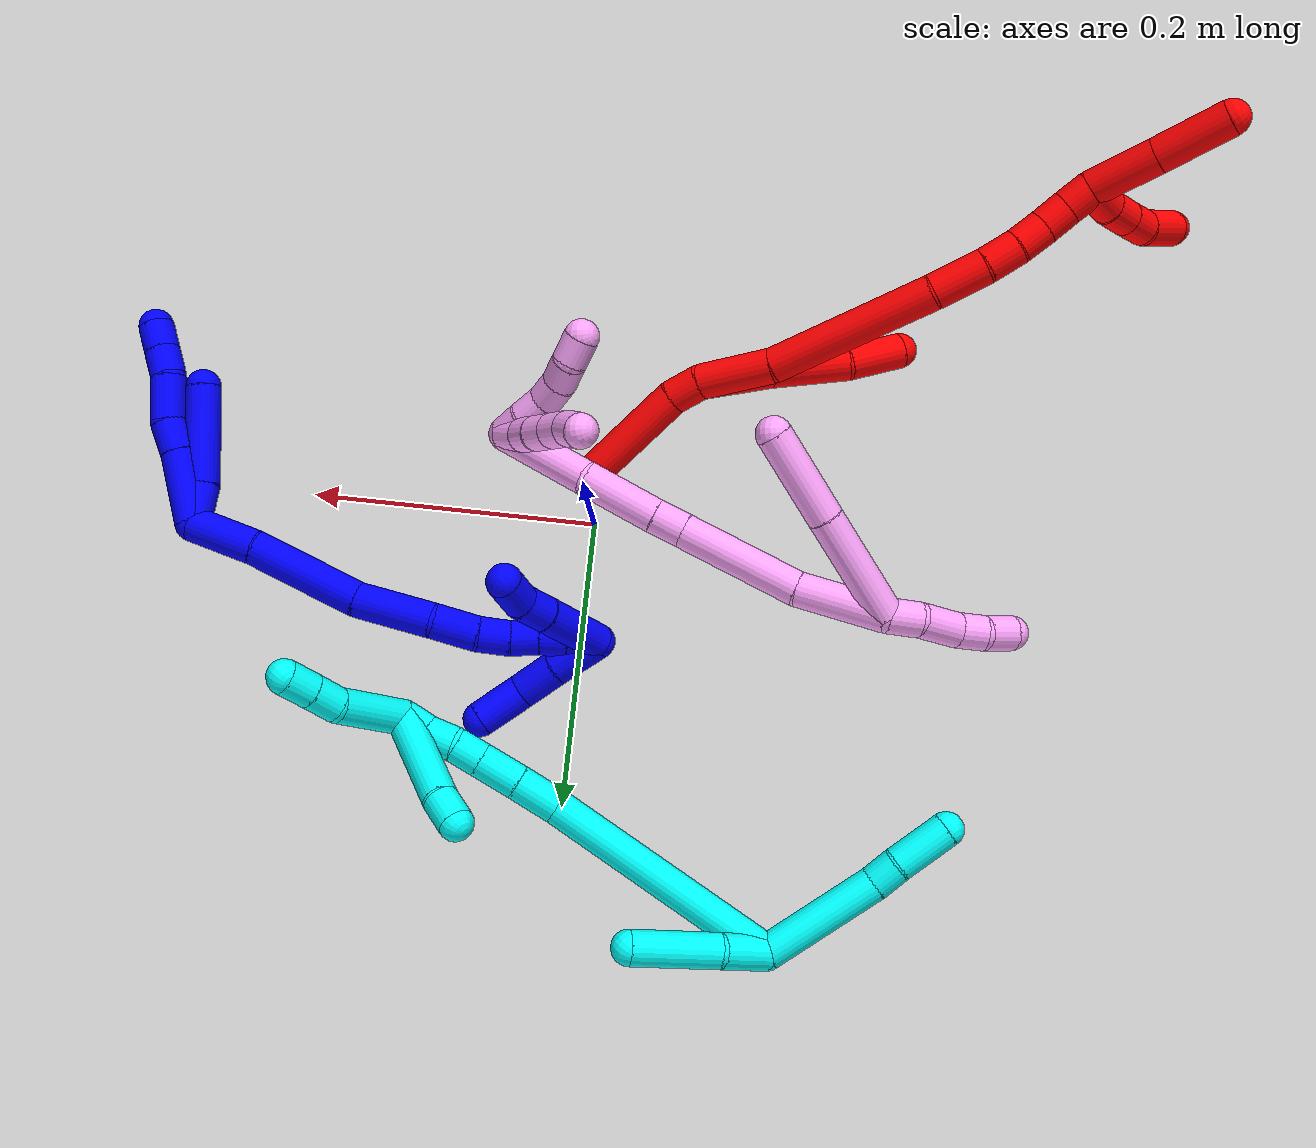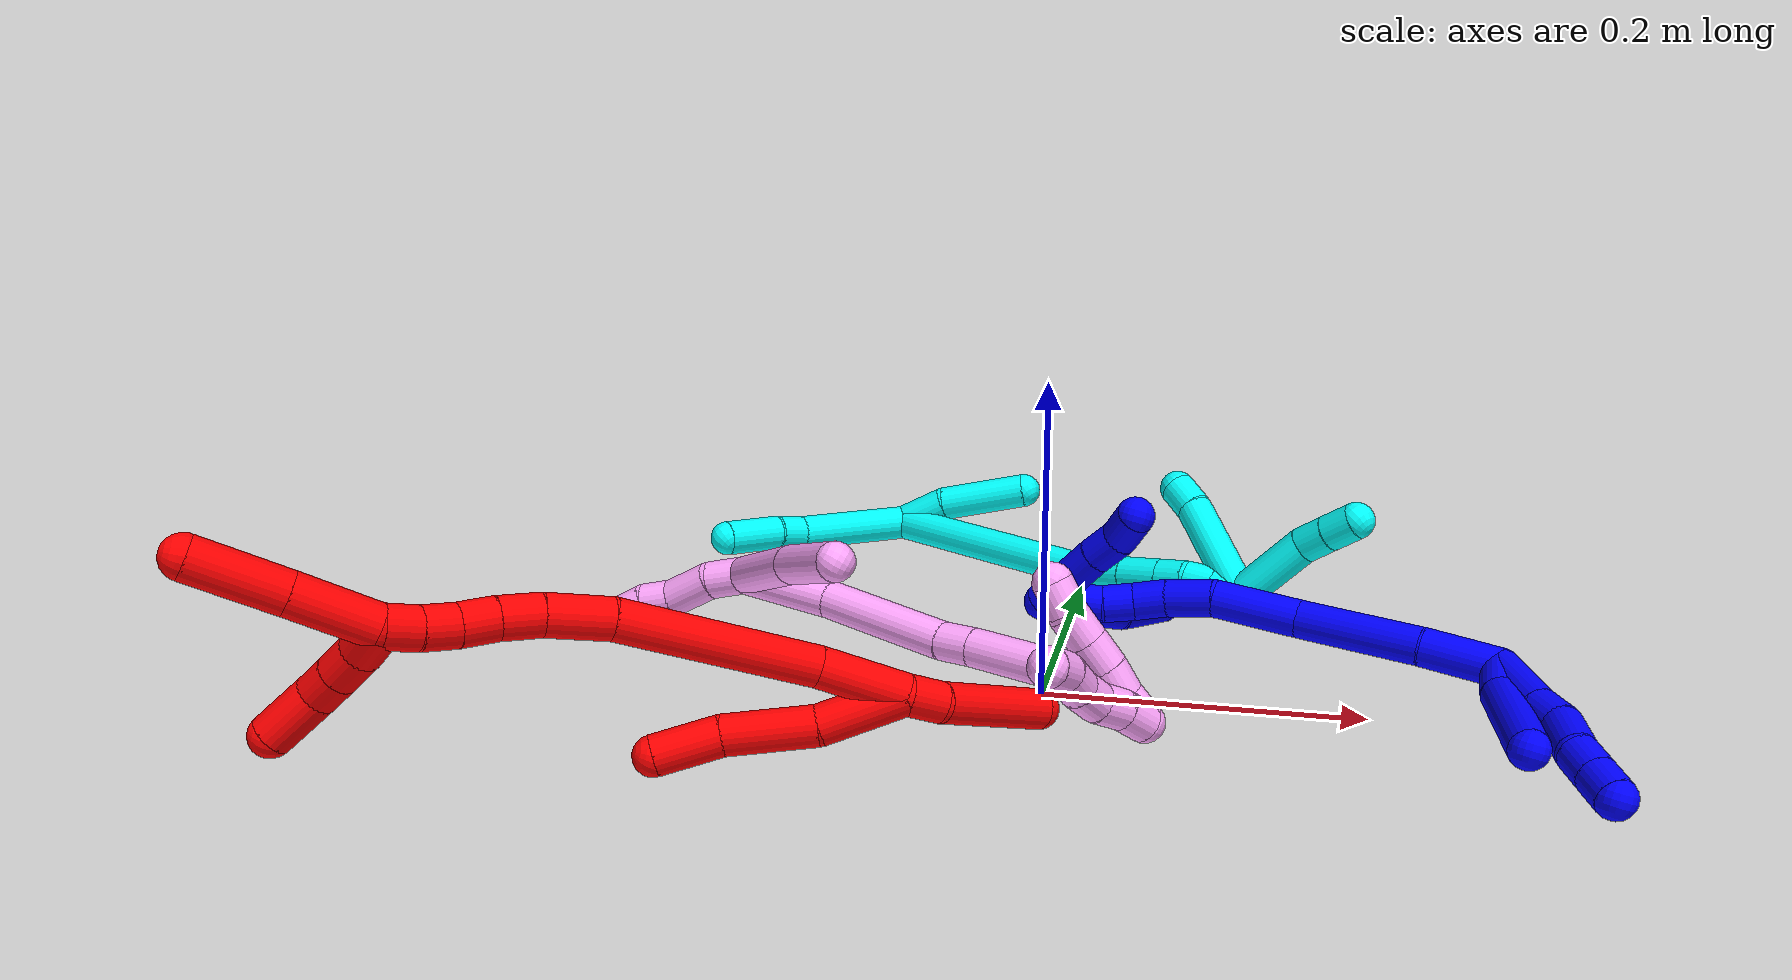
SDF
<sdf version="1.7">
 <world name="default">
  <plugin name="TubeGeneratorPlugin" filename="libtube_generator_plugin.so"/>
  <model name="photoneo_s_sensor">
   <static>1</static>
   <pose>0 0 2 1.57079 1.57079 3.14159</pose>
   <link name="link">
    <inertial><mass>0.1</mass></inertial>
    <sensor name="sensor" type="depth">
     <update_rate>30</update_rate>
     <camera>
      <horizontal_fov>1.22</horizontal_fov>
      <image><width>1920</width><height>1200</height><format>B8G8R8</format></image>
      <clip><near>0.1</near><far>4</far></clip>
      <depth_camera><output>points</output></depth_camera>
     </camera>
     <plugin name="camera_plugin" filename="libgazebo_ros_depth_camera.so">
      <baseline>0.2</baseline>
      <alwaysOn>1</alwaysOn>
      <updateRate>0.0</updateRate>
      <cameraName>camera_ir</cameraName>
      <imageTopicName>/camera/color/image_raw</imageTopicName>
      <cameraInfoTopicName>/camera/color/camera_info</cameraInfoTopicName>
      <depthImageTopicName>/camera/depth/image_raw</depthImageTopicName>
      <depthImageCameraInfoTopicName>/camera/depth/camera_info</depthImageCameraInfoTopicName>
      <pointCloudTopicName>/camera/depth/points</pointCloudTopicName>
      <frameName>fr_optical</frameName>
      <pointCloudCutoff>0.1</pointCloudCutoff>
      <pointCloudCutoffMax>2.0</pointCloudCutoffMax>
      <distortionK1>0</distortionK1>
      <distortionK2>0</distortionK2>
      <distortionK3>0</distortionK3>
      <distortionT1>0</distortionT1>
      <distortionT2>0</distortionT2>
      <CxPrime>0</CxPrime>
      <Cx>0</Cx>
      <Cy>0</Cy>
      <focalLength>0</focalLength>
      <hackBaseline>0</hackBaseline>
     </plugin>
    </sensor>
   </link>
  </model>
  <gravity>0 0 -9.8</gravity>
  <magnetic_field>6e-06 2.3e-05 -4.2e-05</magnetic_field>
  <atmosphere type="adiabatic"/>
  <physics name="default_physics" default="0" type="ode">
   <max_step_size>0.003</max_step_size>
   <real_time_factor>1</real_time_factor>
   <real_time_update_rate>1000</real_time_update_rate>
   <max_contacts>10000</max_contacts>
   <ode>
    <solver>
     <type>quick</type>
     <iters>100</iters>
     <sor>1.3</sor>
     <use_dynamic_moi_rescaling>0</use_dynamic_moi_rescaling>
    </solver>
    <constraints>
     <contact_max_correcting_vel>0</contact_max_correcting_vel>
     <contact_surface_layer>0.001</contact_surface_layer>
     <cfm>0</cfm>
     <erp>0.2</erp>
    </constraints>
   </ode>
  </physics>
  <scene><ambient>0.4 0.4 0.4 1</ambient><background>0.7 0.7 0.7 1</background><shadows>0</shadows></scene>
  <audio><device>default</device></audio>
  <spherical_coordinates>
   <surface_model>EARTH_WGS84</surface_model>
   <latitude_deg>0</latitude_deg>
   <longitude_deg>0</longitude_deg>
   <elevation>0</elevation>
   <heading_deg>0</heading_deg>
  </spherical_coordinates>
  <model name="bin">
   <static>1</static>
   <link name="bottom">
    <collision name="collision-bottom">
     <pose>0 0 -0.01 0 -0 0</pose>
     <geometry><box><size>0.8 0.6 0.02</size></box></geometry>
     <surface>
      <friction><ode><mu>100</mu><mu2>100</mu2></ode></friction>
      <contact><collide_bitmask>65535</collide_bitmask></contact>
     </surface>
    </collision>
   </link>
   <link name="west_wall">
    <collision name="collision-west_wall">
     <pose>-0.41 0 0.1 0 -0 0</pose>
     <geometry><box><size>0.02 0.6 0.2</size></box></geometry>
     <surface>
      <friction><ode><mu>100</mu><mu2>100</mu2></ode></friction>
      <contact><collide_bitmask>65535</collide_bitmask></contact>
     </surface>
    </collision>
   </link>
   <link name="east_wall">
    <collision name="collision-east_wall">
     <pose>0.41 0 0.1 0 -0 0</pose>
     <geometry><box><size>0.02 0.6 0.2</size></box></geometry>
     <surface>
      <friction><ode><mu>100</mu><mu2>100</mu2></ode></friction>
      <contact><collide_bitmask>65535</collide_bitmask></contact>
     </surface>
    </collision>
   </link>
   <link name="south_wall">
    <collision name="collision-south_wall">
     <pose>0 -0.31 0.1 0 -0 0</pose>
     <geometry><box><size>0.8 0.02 0.2</size></box></geometry>
     <surface>
      <friction><ode><mu>100</mu><mu2>100</mu2></ode></friction>
      <contact><collide_bitmask>65535</collide_bitmask></contact>
     </surface>
    </collision>
   </link>
   <link name="north_wall">
    <collision name="collision-north_wall">
     <pose>0 0.31 0.1 0 -0 0</pose>
     <geometry><box><size>0.8 0.02 0.2</size></box></geometry>
     <surface>
      <friction><ode><mu>100</mu><mu2>100</mu2></ode></friction>
      <contact><collide_bitmask>65535</collide_bitmask></contact>
     </surface>
    </collision>
   </link>
  </model>
  <model name="1">
   <static>0</static>
   <link name="1">
    <collision name="collision-cylinder-e_1_2_8">
     <pose>0.003225 -0.02495 -0.007505 1.86299 0.123144 0.165469</pose>
     <geometry><cylinder><radius>0.0125</radius><length>0.052505</length></cylinder></geometry>
     <surface>
      <friction><ode><mu>1.16</mu><mu2>1.16</mu2><slip1>0</slip1><slip2>0</slip2></ode></friction>
      <contact><ode><kp>1e+06</kp><kd>1</kd><max_vel>0</max_vel><min_depth>0.001</min_depth></ode></contact>
     </surface>
    </collision>
    <visual name="visual-cylinder-e_1_2_8">
     <pose>0.003225 -0.02495 -0.007505 1.86299 0.123144 0.165469</pose>
     <geometry><cylinder><radius>0.0125</radius><length>0.052505</length></cylinder></geometry>
     <material><ambient>0 0 1 1</ambient></material>
    </visual>
    <collision name="collision-cylinder-e_2_8_9">
     <pose>0.009026 -0.061025 -0.017525 1.79309 0.22212 0.277287</pose>
     <geometry><cylinder><radius>0.0125</radius><length>0.023388</length></cylinder></geometry>
     <surface>
      <friction><ode><mu>1.16</mu><mu2>1.16</mu2><slip1>0</slip1><slip2>0</slip2></ode></friction>
      <contact><ode><kp>1e+06</kp><kd>1</kd><max_vel>0</max_vel><min_depth>0.001</min_depth></ode></contact>
     </surface>
    </collision>
    <visual name="visual-cylinder-e_2_8_9">
     <pose>0.009026 -0.061025 -0.017525 1.79309 0.22212 0.277287</pose>
     <geometry><cylinder><radius>0.0125</radius><length>0.023388</length></cylinder></geometry>
     <material><ambient>0 0 1 1</ambient></material>
    </visual>
    <collision name="collision-cylinder-e_3_9_10">
     <pose>0.010459 -0.087457 -0.025641 1.92162 -0.070033 -0.100163</pose>
     <geometry><cylinder><radius>0.0125</radius><length>0.032677</length></cylinder></geometry>
     <surface>
      <friction><ode><mu>1.16</mu><mu2>1.16</mu2><slip1>0</slip1><slip2>0</slip2></ode></friction>
      <contact><ode><kp>1e+06</kp><kd>1</kd><max_vel>0</max_vel><min_depth>0.001</min_depth></ode></contact>
     </surface>
    </collision>
    <visual name="visual-cylinder-e_3_9_10">
     <pose>0.010459 -0.087457 -0.025641 1.92162 -0.070033 -0.100163</pose>
     <geometry><cylinder><radius>0.0125</radius><length>0.032677</length></cylinder></geometry>
     <material><ambient>0 0 1 1</ambient></material>
    </visual>
    <collision name="collision-cylinder-e_4_10_11">
     <pose>0.011577 -0.112109 -0.035245 1.97541 0.218864 0.330116</pose>
     <geometry><cylinder><radius>0.0125</radius><length>0.020831</length></cylinder></geometry>
     <surface>
      <friction><ode><mu>1.16</mu><mu2>1.16</mu2><slip1>0</slip1><slip2>0</slip2></ode></friction>
      <contact><ode><kp>1e+06</kp><kd>1</kd><max_vel>0</max_vel><min_depth>0.001</min_depth></ode></contact>
     </surface>
    </collision>
    <visual name="visual-cylinder-e_4_10_11">
     <pose>0.011577 -0.112109 -0.035245 1.97541 0.218864 0.330116</pose>
     <geometry><cylinder><radius>0.0125</radius><length>0.020831</length></cylinder></geometry>
     <material><ambient>0 0 1 1</ambient></material>
    </visual>
    <collision name="collision-cylinder-e_5_11_6">
     <pose>0.016013 -0.130742 -0.043132 1.96699 0.212792 0.318172</pose>
     <geometry><cylinder><radius>0.0125</radius><length>0.020598</length></cylinder></geometry>
     <surface>
      <friction><ode><mu>1.16</mu><mu2>1.16</mu2><slip1>0</slip1><slip2>0</slip2></ode></friction>
      <contact><ode><kp>1e+06</kp><kd>1</kd><max_vel>0</max_vel><min_depth>0.001</min_depth></ode></contact>
     </surface>
    </collision>
    <visual name="visual-cylinder-e_5_11_6">
     <pose>0.016013 -0.130742 -0.043132 1.96699 0.212792 0.318172</pose>
     <geometry><cylinder><radius>0.0125</radius><length>0.020598</length></cylinder></geometry>
     <material><ambient>0 0 1 1</ambient></material>
    </visual>
    <collision name="collision-cylinder-e_1_2_12">
     <pose>-0.002894 -0.012166 -0.007379 2.11595 -0.20063 -0.353781</pose>
     <geometry><cylinder><radius>0.0125</radius><length>0.029041</length></cylinder></geometry>
     <surface>
      <friction><ode><mu>1.16</mu><mu2>1.16</mu2><slip1>0</slip1><slip2>0</slip2></ode></friction>
      <contact><ode><kp>1e+06</kp><kd>1</kd><max_vel>0</max_vel><min_depth>0.001</min_depth></ode></contact>
     </surface>
    </collision>
    <visual name="visual-cylinder-e_1_2_12">
     <pose>-0.002894 -0.012166 -0.007379 2.11595 -0.20063 -0.353781</pose>
     <geometry><cylinder><radius>0.0125</radius><length>0.029041</length></cylinder></geometry>
     <material><ambient>0 0 1 1</ambient></material>
    </visual>
    <collision name="collision-cylinder-e_2_12_5">
     <pose>-0.009142 -0.057803 -0.026041 1.89597 -0.09468 -0.131745</pose>
     <geometry><cylinder><radius>0.0125</radius><length>0.070959</length></cylinder></geometry>
     <surface>
      <friction><ode><mu>1.16</mu><mu2>1.16</mu2><slip1>0</slip1><slip2>0</slip2></ode></friction>
      <contact><ode><kp>1e+06</kp><kd>1</kd><max_vel>0</max_vel><min_depth>0.001</min_depth></ode></contact>
     </surface>
    </collision>
    <visual name="visual-cylinder-e_2_12_5">
     <pose>-0.009142 -0.057803 -0.026041 1.89597 -0.09468 -0.131745</pose>
     <geometry><cylinder><radius>0.0125</radius><length>0.070959</length></cylinder></geometry>
     <material><ambient>0 0 1 1</ambient></material>
    </visual>
    <collision name="collision-cylinder-e_1_2_13">
     <pose>-0.020964 0.012268 -0.000775 -1.63389 -1.04047 1.09579</pose>
     <geometry><cylinder><radius>0.0125</radius><length>0.048603</length></cylinder></geometry>
     <surface>
      <friction><ode><mu>1.16</mu><mu2>1.16</mu2><slip1>0</slip1><slip2>0</slip2></ode></friction>
      <contact><ode><kp>1e+06</kp><kd>1</kd><max_vel>0</max_vel><min_depth>0.001</min_depth></ode></contact>
     </surface>
    </collision>
    <visual name="visual-cylinder-e_1_2_13">
     <pose>-0.020964 0.012268 -0.000775 -1.63389 -1.04047 1.09579</pose>
     <geometry><cylinder><radius>0.0125</radius><length>0.048603</length></cylinder></geometry>
     <material><ambient>0 0 1 1</ambient></material>
    </visual>
    <collision name="collision-cylinder-e_2_13_14">
     <pose>-0.073952 0.048899 -0.004498 -1.6912 -0.916918 1.01616</pose>
     <geometry><cylinder><radius>0.0125</radius><length>0.080694</length></cylinder></geometry>
     <surface>
      <friction><ode><mu>1.16</mu><mu2>1.16</mu2><slip1>0</slip1><slip2>0</slip2></ode></friction>
      <contact><ode><kp>1e+06</kp><kd>1</kd><max_vel>0</max_vel><min_depth>0.001</min_depth></ode></contact>
     </surface>
    </collision>
    <visual name="visual-cylinder-e_2_13_14">
     <pose>-0.073952 0.048899 -0.004498 -1.6912 -0.916918 1.01616</pose>
     <geometry><cylinder><radius>0.0125</radius><length>0.080694</length></cylinder></geometry>
     <material><ambient>0 0 1 1</ambient></material>
    </visual>
    <collision name="collision-cylinder-e_3_14_15">
     <pose>-0.13126 0.085117 -0.008991 -1.70047 -1.12915 1.24976</pose>
     <geometry><cylinder><radius>0.0125</radius><length>0.055933</length></cylinder></geometry>
     <surface>
      <friction><ode><mu>1.16</mu><mu2>1.16</mu2><slip1>0</slip1><slip2>0</slip2></ode></friction>
      <contact><ode><kp>1e+06</kp><kd>1</kd><max_vel>0</max_vel><min_depth>0.001</min_depth></ode></contact>
     </surface>
    </collision>
    <visual name="visual-cylinder-e_3_14_15">
     <pose>-0.13126 0.085117 -0.008991 -1.70047 -1.12915 1.24976</pose>
     <geometry><cylinder><radius>0.0125</radius><length>0.055933</length></cylinder></geometry>
     <material><ambient>0 0 1 1</ambient></material>
    </visual>
    <collision name="collision-cylinder-e_4_15_16">
     <pose>-0.169593 0.104642 -0.014896 -2.08752 -0.976257 1.47929</pose>
     <geometry><cylinder><radius>0.0125</radius><length>0.031506</length></cylinder></geometry>
     <surface>
      <friction><ode><mu>1.16</mu><mu2>1.16</mu2><slip1>0</slip1><slip2>0</slip2></ode></friction>
      <contact><ode><kp>1e+06</kp><kd>1</kd><max_vel>0</max_vel><min_depth>0.001</min_depth></ode></contact>
     </surface>
    </collision>
    <visual name="visual-cylinder-e_4_15_16">
     <pose>-0.169593 0.104642 -0.014896 -2.08752 -0.976257 1.47929</pose>
     <geometry><cylinder><radius>0.0125</radius><length>0.031506</length></cylinder></geometry>
     <material><ambient>0 0 1 1</ambient></material>
    </visual>
    <collision name="collision-cylinder-e_5_16_17">
     <pose>-0.192129 0.116311 -0.023665 -2.40513 -1.01044 1.9234</pose>
     <geometry><cylinder><radius>0.0125</radius><length>0.022398</length></cylinder></geometry>
     <surface>
      <friction><ode><mu>1.16</mu><mu2>1.16</mu2><slip1>0</slip1><slip2>0</slip2></ode></friction>
      <contact><ode><kp>1e+06</kp><kd>1</kd><max_vel>0</max_vel><min_depth>0.001</min_depth></ode></contact>
     </surface>
    </collision>
    <visual name="visual-cylinder-e_5_16_17">
     <pose>-0.192129 0.116311 -0.023665 -2.40513 -1.01044 1.9234</pose>
     <geometry><cylinder><radius>0.0125</radius><length>0.022398</length></cylinder></geometry>
     <material><ambient>0 0 1 1</ambient></material>
    </visual>
    <collision name="collision-cylinder-e_6_17_18">
     <pose>-0.211014 0.12217 -0.031751 -2.67298 -1.15762 2.44118</pose>
     <geometry><cylinder><radius>0.0125</radius><length>0.020524</length></cylinder></geometry>
     <surface>
      <friction><ode><mu>1.16</mu><mu2>1.16</mu2><slip1>0</slip1><slip2>0</slip2></ode></friction>
      <contact><ode><kp>1e+06</kp><kd>1</kd><max_vel>0</max_vel><min_depth>0.001</min_depth></ode></contact>
     </surface>
    </collision>
    <visual name="visual-cylinder-e_6_17_18">
     <pose>-0.211014 0.12217 -0.031751 -2.67298 -1.15762 2.44118</pose>
     <geometry><cylinder><radius>0.0125</radius><length>0.020524</length></cylinder></geometry>
     <material><ambient>0 0 1 1</ambient></material>
    </visual>
    <collision name="collision-cylinder-e_7_18_19">
     <pose>-0.229741 0.126781 -0.037906 -2.3043 -1.19299 1.98141</pose>
     <geometry><cylinder><radius>0.0125</radius><length>0.020074</length></cylinder></geometry>
     <surface>
      <friction><ode><mu>1.16</mu><mu2>1.16</mu2><slip1>0</slip1><slip2>0</slip2></ode></friction>
      <contact><ode><kp>1e+06</kp><kd>1</kd><max_vel>0</max_vel><min_depth>0.001</min_depth></ode></contact>
     </surface>
    </collision>
    <visual name="visual-cylinder-e_7_18_19">
     <pose>-0.229741 0.126781 -0.037906 -2.3043 -1.19299 1.98141</pose>
     <geometry><cylinder><radius>0.0125</radius><length>0.020074</length></cylinder></geometry>
     <material><ambient>0 0 1 1</ambient></material>
    </visual>
    <collision name="collision-cylinder-e_8_19_1">
     <pose>-0.248446 0.132388 -0.042963 -2.30508 -1.18136 1.97085</pose>
     <geometry><cylinder><radius>0.0125</radius><length>0.020268</length></cylinder></geometry>
     <surface>
      <friction><ode><mu>1.16</mu><mu2>1.16</mu2><slip1>0</slip1><slip2>0</slip2></ode></friction>
      <contact><ode><kp>1e+06</kp><kd>1</kd><max_vel>0</max_vel><min_depth>0.001</min_depth></ode></contact>
     </surface>
    </collision>
    <visual name="visual-cylinder-e_8_19_1">
     <pose>-0.248446 0.132388 -0.042963 -2.30508 -1.18136 1.97085</pose>
     <geometry><cylinder><radius>0.0125</radius><length>0.020268</length></cylinder></geometry>
     <material><ambient>0 0 1 1</ambient></material>
    </visual>
    <collision name="collision-cylinder-e_1_1_20">
     <pose>-0.241592 0.141813 -0.043586 -1.28155 1.17118 -0.918597</pose>
     <geometry><cylinder><radius>0.0125</radius><length>0.035234</length></cylinder></geometry>
     <surface>
      <friction><ode><mu>1.16</mu><mu2>1.16</mu2><slip1>0</slip1><slip2>0</slip2></ode></friction>
      <contact><ode><kp>1e+06</kp><kd>1</kd><max_vel>0</max_vel><min_depth>0.001</min_depth></ode></contact>
     </surface>
    </collision>
    <visual name="visual-cylinder-e_1_1_20">
     <pose>-0.241592 0.141813 -0.043586 -1.28155 1.17118 -0.918597</pose>
     <geometry><cylinder><radius>0.0125</radius><length>0.035234</length></cylinder></geometry>
     <material><ambient>0 0 1 1</ambient></material>
    </visual>
    <collision name="collision-cylinder-e_2_20_21">
     <pose>-0.21167 0.154442 -0.040263 -1.34873 1.14488 -0.951369</pose>
     <geometry><cylinder><radius>0.0125</radius><length>0.030072</length></cylinder></geometry>
     <surface>
      <friction><ode><mu>1.16</mu><mu2>1.16</mu2><slip1>0</slip1><slip2>0</slip2></ode></friction>
      <contact><ode><kp>1e+06</kp><kd>1</kd><max_vel>0</max_vel><min_depth>0.001</min_depth></ode></contact>
     </surface>
    </collision>
    <visual name="visual-cylinder-e_2_20_21">
     <pose>-0.21167 0.154442 -0.040263 -1.34873 1.14488 -0.951369</pose>
     <geometry><cylinder><radius>0.0125</radius><length>0.030072</length></cylinder></geometry>
     <material><ambient>0 0 1 1</ambient></material>
    </visual>
    <collision name="collision-cylinder-e_3_21_4">
     <pose>-0.183098 0.166852 -0.032634 -0.792554 1.0309 -0.465499</pose>
     <geometry><cylinder><radius>0.0125</radius><length>0.034695</length></cylinder></geometry>
     <surface>
      <friction><ode><mu>1.16</mu><mu2>1.16</mu2><slip1>0</slip1><slip2>0</slip2></ode></friction>
      <contact><ode><kp>1e+06</kp><kd>1</kd><max_vel>0</max_vel><min_depth>0.001</min_depth></ode></contact>
     </surface>
    </collision>
    <visual name="visual-cylinder-e_3_21_4">
     <pose>-0.183098 0.166852 -0.032634 -0.792554 1.0309 -0.465499</pose>
     <geometry><cylinder><radius>0.0125</radius><length>0.034695</length></cylinder></geometry>
     <material><ambient>0 0 1 1</ambient></material>
    </visual>
    <collision name="collision-cylinder-e_1_1_22">
     <pose>-0.248546 0.119599 -0.025488 0.662529 0.349664 0.121354</pose>
     <geometry><cylinder><radius>0.0125</radius><length>0.054143</length></cylinder></geometry>
     <surface>
      <friction><ode><mu>1.16</mu><mu2>1.16</mu2><slip1>0</slip1><slip2>0</slip2></ode></friction>
      <contact><ode><kp>1e+06</kp><kd>1</kd><max_vel>0</max_vel><min_depth>0.001</min_depth></ode></contact>
     </surface>
    </collision>
    <visual name="visual-cylinder-e_1_1_22">
     <pose>-0.248546 0.119599 -0.025488 0.662529 0.349664 0.121354</pose>
     <geometry><cylinder><radius>0.0125</radius><length>0.054143</length></cylinder></geometry>
     <material><ambient>0 0 1 1</ambient></material>
    </visual>
    <collision name="collision-cylinder-e_2_22_23">
     <pose>-0.234861 0.097451 0.00228 0.700352 0.412098 0.152381</pose>
     <geometry><cylinder><radius>0.0125</radius><length>0.022027</length></cylinder></geometry>
     <surface>
      <friction><ode><mu>1.16</mu><mu2>1.16</mu2><slip1>0</slip1><slip2>0</slip2></ode></friction>
      <contact><ode><kp>1e+06</kp><kd>1</kd><max_vel>0</max_vel><min_depth>0.001</min_depth></ode></contact>
     </surface>
    </collision>
    <visual name="visual-cylinder-e_2_22_23">
     <pose>-0.234861 0.097451 0.00228 0.700352 0.412098 0.152381</pose>
     <geometry><cylinder><radius>0.0125</radius><length>0.022027</length></cylinder></geometry>
     <material><ambient>0 0 1 1</ambient></material>
    </visual>
    <collision name="collision-cylinder-e_3_23_3">
     <pose>-0.229368 0.082334 0.018158 0.812288 0.090877 0.039104</pose>
     <geometry><cylinder><radius>0.0125</radius><length>0.02383</length></cylinder></geometry>
     <surface>
      <friction><ode><mu>1.16</mu><mu2>1.16</mu2><slip1>0</slip1><slip2>0</slip2></ode></friction>
      <contact><ode><kp>1e+06</kp><kd>1</kd><max_vel>0</max_vel><min_depth>0.001</min_depth></ode></contact>
     </surface>
    </collision>
    <visual name="visual-cylinder-e_3_23_3">
     <pose>-0.229368 0.082334 0.018158 0.812288 0.090877 0.039104</pose>
     <geometry><cylinder><radius>0.0125</radius><length>0.02383</length></cylinder></geometry>
     <material><ambient>0 0 1 1</ambient></material>
    </visual>
    <collision name="collision-sphere-3">
     <pose>-0.228287 0.073721 0.02632 0 -0 0</pose>
     <geometry><sphere><radius>0.0125</radius></sphere></geometry>
     <surface>
      <friction><ode><mu>1.16</mu><mu2>1.16</mu2><slip1>0</slip1><slip2>0</slip2></ode></friction>
      <contact><ode><kp>1e+06</kp><kd>1</kd><max_vel>0</max_vel><min_depth>0.001</min_depth></ode></contact>
     </surface>
    </collision>
    <visual name="visual-sphere-3">
     <pose>-0.228287 0.073721 0.02632 0 -0 0</pose>
     <geometry><sphere><radius>0.0125</radius></sphere></geometry>
     <material><ambient>0 0 1 1</ambient></material>
    </visual>
    <collision name="collision-sphere-23">
     <pose>-0.23045 0.090948 0.009996 0 -0 0</pose>
     <geometry><sphere><radius>0.0125</radius></sphere></geometry>
     <surface>
      <friction><ode><mu>1.16</mu><mu2>1.16</mu2><slip1>0</slip1><slip2>0</slip2></ode></friction>
      <contact><ode><kp>1e+06</kp><kd>1</kd><max_vel>0</max_vel><min_depth>0.001</min_depth></ode></contact>
     </surface>
    </collision>
    <visual name="visual-sphere-23">
     <pose>-0.23045 0.090948 0.009996 0 -0 0</pose>
     <geometry><sphere><radius>0.0125</radius></sphere></geometry>
     <material><ambient>0 0 1 1</ambient></material>
    </visual>
    <collision name="collision-sphere-22">
     <pose>-0.239272 0.103955 -0.005436 0 -0 0</pose>
     <geometry><sphere><radius>0.0125</radius></sphere></geometry>
     <surface>
      <friction><ode><mu>1.16</mu><mu2>1.16</mu2><slip1>0</slip1><slip2>0</slip2></ode></friction>
      <contact><ode><kp>1e+06</kp><kd>1</kd><max_vel>0</max_vel><min_depth>0.001</min_depth></ode></contact>
     </surface>
    </collision>
    <visual name="visual-sphere-22">
     <pose>-0.239272 0.103955 -0.005436 0 -0 0</pose>
     <geometry><sphere><radius>0.0125</radius></sphere></geometry>
     <material><ambient>0 0 1 1</ambient></material>
    </visual>
    <collision name="collision-sphere-4">
     <pose>-0.168218 0.173202 -0.026374 0 -0 0</pose>
     <geometry><sphere><radius>0.0125</radius></sphere></geometry>
     <surface>
      <friction><ode><mu>1.16</mu><mu2>1.16</mu2><slip1>0</slip1><slip2>0</slip2></ode></friction>
      <contact><ode><kp>1e+06</kp><kd>1</kd><max_vel>0</max_vel><min_depth>0.001</min_depth></ode></contact>
     </surface>
    </collision>
    <visual name="visual-sphere-4">
     <pose>-0.168218 0.173202 -0.026374 0 -0 0</pose>
     <geometry><sphere><radius>0.0125</radius></sphere></geometry>
     <material><ambient>0 0 1 1</ambient></material>
    </visual>
    <collision name="collision-sphere-21">
     <pose>-0.197978 0.160501 -0.038894 0 -0 0</pose>
     <geometry><sphere><radius>0.0125</radius></sphere></geometry>
     <surface>
      <friction><ode><mu>1.16</mu><mu2>1.16</mu2><slip1>0</slip1><slip2>0</slip2></ode></friction>
      <contact><ode><kp>1e+06</kp><kd>1</kd><max_vel>0</max_vel><min_depth>0.001</min_depth></ode></contact>
     </surface>
    </collision>
    <visual name="visual-sphere-21">
     <pose>-0.197978 0.160501 -0.038894 0 -0 0</pose>
     <geometry><sphere><radius>0.0125</radius></sphere></geometry>
     <material><ambient>0 0 1 1</ambient></material>
    </visual>
    <collision name="collision-sphere-20">
     <pose>-0.225363 0.148382 -0.041631 0 -0 0</pose>
     <geometry><sphere><radius>0.0125</radius></sphere></geometry>
     <surface>
      <friction><ode><mu>1.16</mu><mu2>1.16</mu2><slip1>0</slip1><slip2>0</slip2></ode></friction>
      <contact><ode><kp>1e+06</kp><kd>1</kd><max_vel>0</max_vel><min_depth>0.001</min_depth></ode></contact>
     </surface>
    </collision>
    <visual name="visual-sphere-20">
     <pose>-0.225363 0.148382 -0.041631 0 -0 0</pose>
     <geometry><sphere><radius>0.0125</radius></sphere></geometry>
     <material><ambient>0 0 1 1</ambient></material>
    </visual>
    <collision name="collision-sphere-6">
     <pose>0.018188 -0.140029 -0.047017 0 -0 0</pose>
     <geometry><sphere><radius>0.0125</radius></sphere></geometry>
     <surface>
      <friction><ode><mu>1.16</mu><mu2>1.16</mu2><slip1>0</slip1><slip2>0</slip2></ode></friction>
      <contact><ode><kp>1e+06</kp><kd>1</kd><max_vel>0</max_vel><min_depth>0.001</min_depth></ode></contact>
     </surface>
    </collision>
    <visual name="visual-sphere-6">
     <pose>0.018188 -0.140029 -0.047017 0 -0 0</pose>
     <geometry><sphere><radius>0.0125</radius></sphere></geometry>
     <material><ambient>0 0 1 1</ambient></material>
    </visual>
    <collision name="collision-sphere-11">
     <pose>0.013838 -0.121455 -0.039247 0 -0 0</pose>
     <geometry><sphere><radius>0.0125</radius></sphere></geometry>
     <surface>
      <friction><ode><mu>1.16</mu><mu2>1.16</mu2><slip1>0</slip1><slip2>0</slip2></ode></friction>
      <contact><ode><kp>1e+06</kp><kd>1</kd><max_vel>0</max_vel><min_depth>0.001</min_depth></ode></contact>
     </surface>
    </collision>
    <visual name="visual-sphere-11">
     <pose>0.013838 -0.121455 -0.039247 0 -0 0</pose>
     <geometry><sphere><radius>0.0125</radius></sphere></geometry>
     <material><ambient>0 0 1 1</ambient></material>
    </visual>
    <collision name="collision-sphere-10">
     <pose>0.009315 -0.102763 -0.031243 0 -0 0</pose>
     <geometry><sphere><radius>0.0125</radius></sphere></geometry>
     <surface>
      <friction><ode><mu>1.16</mu><mu2>1.16</mu2><slip1>0</slip1><slip2>0</slip2></ode></friction>
      <contact><ode><kp>1e+06</kp><kd>1</kd><max_vel>0</max_vel><min_depth>0.001</min_depth></ode></contact>
     </surface>
    </collision>
    <visual name="visual-sphere-10">
     <pose>0.009315 -0.102763 -0.031243 0 -0 0</pose>
     <geometry><sphere><radius>0.0125</radius></sphere></geometry>
     <material><ambient>0 0 1 1</ambient></material>
    </visual>
    <collision name="collision-sphere-9">
     <pose>0.011602 -0.072152 -0.02004 0 -0 0</pose>
     <geometry><sphere><radius>0.0125</radius></sphere></geometry>
     <surface>
      <friction><ode><mu>1.16</mu><mu2>1.16</mu2><slip1>0</slip1><slip2>0</slip2></ode></friction>
      <contact><ode><kp>1e+06</kp><kd>1</kd><max_vel>0</max_vel><min_depth>0.001</min_depth></ode></contact>
     </surface>
    </collision>
    <visual name="visual-sphere-9">
     <pose>0.011602 -0.072152 -0.02004 0 -0 0</pose>
     <geometry><sphere><radius>0.0125</radius></sphere></geometry>
     <material><ambient>0 0 1 1</ambient></material>
    </visual>
    <collision name="collision-sphere-2">
     <geometry><sphere><radius>0.0125</radius></sphere></geometry>
     <surface>
      <friction><ode><mu>1.16</mu><mu2>1.16</mu2><slip1>0</slip1><slip2>0</slip2></ode></friction>
      <contact><ode><kp>1e+06</kp><kd>1</kd><max_vel>0</max_vel><min_depth>0.001</min_depth></ode></contact>
     </surface>
    </collision>
    <visual name="visual-sphere-2">
     <geometry><sphere><radius>0.0125</radius></sphere></geometry>
     <material><ambient>0 0 1 1</ambient></material>
    </visual>
    <collision name="collision-sphere-19">
     <pose>-0.23907 0.129532 -0.040385 0 -0 0</pose>
     <geometry><sphere><radius>0.0125</radius></sphere></geometry>
     <surface>
      <friction><ode><mu>1.16</mu><mu2>1.16</mu2><slip1>0</slip1><slip2>0</slip2></ode></friction>
      <contact><ode><kp>1e+06</kp><kd>1</kd><max_vel>0</max_vel><min_depth>0.001</min_depth></ode></contact>
     </surface>
    </collision>
    <visual name="visual-sphere-19">
     <pose>-0.23907 0.129532 -0.040385 0 -0 0</pose>
     <geometry><sphere><radius>0.0125</radius></sphere></geometry>
     <material><ambient>0 0 1 1</ambient></material>
    </visual>
    <collision name="collision-sphere-8">
     <pose>0.006449 -0.049899 -0.01501 0 -0 0</pose>
     <geometry><sphere><radius>0.0125</radius></sphere></geometry>
     <surface>
      <friction><ode><mu>1.16</mu><mu2>1.16</mu2><slip1>0</slip1><slip2>0</slip2></ode></friction>
      <contact><ode><kp>1e+06</kp><kd>1</kd><max_vel>0</max_vel><min_depth>0.001</min_depth></ode></contact>
     </surface>
    </collision>
    <visual name="visual-sphere-8">
     <pose>0.006449 -0.049899 -0.01501 0 -0 0</pose>
     <geometry><sphere><radius>0.0125</radius></sphere></geometry>
     <material><ambient>0 0 1 1</ambient></material>
    </visual>
    <collision name="collision-sphere-12">
     <pose>-0.005787 -0.024333 -0.014757 0 -0 0</pose>
     <geometry><sphere><radius>0.0125</radius></sphere></geometry>
     <surface>
      <friction><ode><mu>1.16</mu><mu2>1.16</mu2><slip1>0</slip1><slip2>0</slip2></ode></friction>
      <contact><ode><kp>1e+06</kp><kd>1</kd><max_vel>0</max_vel><min_depth>0.001</min_depth></ode></contact>
     </surface>
    </collision>
    <visual name="visual-sphere-12">
     <pose>-0.005787 -0.024333 -0.014757 0 -0 0</pose>
     <geometry><sphere><radius>0.0125</radius></sphere></geometry>
     <material><ambient>0 0 1 1</ambient></material>
    </visual>
    <collision name="collision-sphere-5">
     <pose>-0.012496 -0.091273 -0.037325 0 -0 0</pose>
     <geometry><sphere><radius>0.0125</radius></sphere></geometry>
     <surface>
      <friction><ode><mu>1.16</mu><mu2>1.16</mu2><slip1>0</slip1><slip2>0</slip2></ode></friction>
      <contact><ode><kp>1e+06</kp><kd>1</kd><max_vel>0</max_vel><min_depth>0.001</min_depth></ode></contact>
     </surface>
    </collision>
    <visual name="visual-sphere-5">
     <pose>-0.012496 -0.091273 -0.037325 0 -0 0</pose>
     <geometry><sphere><radius>0.0125</radius></sphere></geometry>
     <material><ambient>0 0 1 1</ambient></material>
    </visual>
    <collision name="collision-sphere-13">
     <pose>-0.041927 0.024535 -0.00155 0 -0 0</pose>
     <geometry><sphere><radius>0.0125</radius></sphere></geometry>
     <surface>
      <friction><ode><mu>1.16</mu><mu2>1.16</mu2><slip1>0</slip1><slip2>0</slip2></ode></friction>
      <contact><ode><kp>1e+06</kp><kd>1</kd><max_vel>0</max_vel><min_depth>0.001</min_depth></ode></contact>
     </surface>
    </collision>
    <visual name="visual-sphere-13">
     <pose>-0.041927 0.024535 -0.00155 0 -0 0</pose>
     <geometry><sphere><radius>0.0125</radius></sphere></geometry>
     <material><ambient>0 0 1 1</ambient></material>
    </visual>
    <collision name="collision-sphere-14">
     <pose>-0.105977 0.073263 -0.007446 0 -0 0</pose>
     <geometry><sphere><radius>0.0125</radius></sphere></geometry>
     <surface>
      <friction><ode><mu>1.16</mu><mu2>1.16</mu2><slip1>0</slip1><slip2>0</slip2></ode></friction>
      <contact><ode><kp>1e+06</kp><kd>1</kd><max_vel>0</max_vel><min_depth>0.001</min_depth></ode></contact>
     </surface>
    </collision>
    <visual name="visual-sphere-14">
     <pose>-0.105977 0.073263 -0.007446 0 -0 0</pose>
     <geometry><sphere><radius>0.0125</radius></sphere></geometry>
     <material><ambient>0 0 1 1</ambient></material>
    </visual>
    <collision name="collision-sphere-15">
     <pose>-0.156543 0.09697 -0.010537 0 -0 0</pose>
     <geometry><sphere><radius>0.0125</radius></sphere></geometry>
     <surface>
      <friction><ode><mu>1.16</mu><mu2>1.16</mu2><slip1>0</slip1><slip2>0</slip2></ode></friction>
      <contact><ode><kp>1e+06</kp><kd>1</kd><max_vel>0</max_vel><min_depth>0.001</min_depth></ode></contact>
     </surface>
    </collision>
    <visual name="visual-sphere-15">
     <pose>-0.156543 0.09697 -0.010537 0 -0 0</pose>
     <geometry><sphere><radius>0.0125</radius></sphere></geometry>
     <material><ambient>0 0 1 1</ambient></material>
    </visual>
    <collision name="collision-sphere-16">
     <pose>-0.182643 0.112313 -0.019255 0 -0 0</pose>
     <geometry><sphere><radius>0.0125</radius></sphere></geometry>
     <surface>
      <friction><ode><mu>1.16</mu><mu2>1.16</mu2><slip1>0</slip1><slip2>0</slip2></ode></friction>
      <contact><ode><kp>1e+06</kp><kd>1</kd><max_vel>0</max_vel><min_depth>0.001</min_depth></ode></contact>
     </surface>
    </collision>
    <visual name="visual-sphere-16">
     <pose>-0.182643 0.112313 -0.019255 0 -0 0</pose>
     <geometry><sphere><radius>0.0125</radius></sphere></geometry>
     <material><ambient>0 0 1 1</ambient></material>
    </visual>
    <collision name="collision-sphere-17">
     <pose>-0.201615 0.120309 -0.028075 0 -0 0</pose>
     <geometry><sphere><radius>0.0125</radius></sphere></geometry>
     <surface>
      <friction><ode><mu>1.16</mu><mu2>1.16</mu2><slip1>0</slip1><slip2>0</slip2></ode></friction>
      <contact><ode><kp>1e+06</kp><kd>1</kd><max_vel>0</max_vel><min_depth>0.001</min_depth></ode></contact>
     </surface>
    </collision>
    <visual name="visual-sphere-17">
     <pose>-0.201615 0.120309 -0.028075 0 -0 0</pose>
     <geometry><sphere><radius>0.0125</radius></sphere></geometry>
     <material><ambient>0 0 1 1</ambient></material>
    </visual>
    <collision name="collision-sphere-18">
     <pose>-0.220412 0.124031 -0.035427 0 -0 0</pose>
     <geometry><sphere><radius>0.0125</radius></sphere></geometry>
     <surface>
      <friction><ode><mu>1.16</mu><mu2>1.16</mu2><slip1>0</slip1><slip2>0</slip2></ode></friction>
      <contact><ode><kp>1e+06</kp><kd>1</kd><max_vel>0</max_vel><min_depth>0.001</min_depth></ode></contact>
     </surface>
    </collision>
    <visual name="visual-sphere-18">
     <pose>-0.220412 0.124031 -0.035427 0 -0 0</pose>
     <geometry><sphere><radius>0.0125</radius></sphere></geometry>
     <material><ambient>0 0 1 1</ambient></material>
    </visual>
    <collision name="collision-sphere-1">
     <pose>-0.257821 0.135244 -0.045541 0 -0 0</pose>
     <geometry><sphere><radius>0.0125</radius></sphere></geometry>
     <surface>
      <friction><ode><mu>1.16</mu><mu2>1.16</mu2><slip1>0</slip1><slip2>0</slip2></ode></friction>
      <contact><ode><kp>1e+06</kp><kd>1</kd><max_vel>0</max_vel><min_depth>0.001</min_depth></ode></contact>
     </surface>
    </collision>
    <visual name="visual-sphere-1">
     <pose>-0.257821 0.135244 -0.045541 0 -0 0</pose>
     <geometry><sphere><radius>0.0125</radius></sphere></geometry>
     <material><ambient>0 0 1 1</ambient></material>
    </visual>
    <inertial>
     <pose>-0.110291 0.045168 -0.019051 0 -0 0</pose>
     <mass>0.75</mass>
     <inertia><ixx>0.000125</ixx><ixy>0</ixy><ixz>0</ixz><iyy>9.5e-05</iyy><iyz>0</iyz><izz>6.8e-05</izz></inertia>
    </inertial>
   </link>
   <pose>0.277358 0.033065 0.027206 -0.256691 0.305221 0.241782</pose>
  </model>
  <model name="2">
   <static>0</static>
   <link name="2">
    <collision name="collision-cylinder-e_1_2_8">
     <pose>-0.016802 -0.004725 0.020211 0.229642 -0.680503 -0.081612</pose>
     <geometry><cylinder><radius>0.0125</radius><length>0.053408</length></cylinder></geometry>
     <surface>
      <friction><ode><mu>1.16</mu><mu2>1.16</mu2><slip1>0</slip1><slip2>0</slip2></ode></friction>
      <contact><ode><kp>1e+06</kp><kd>1</kd><max_vel>0</max_vel><min_depth>0.001</min_depth></ode></contact>
     </surface>
    </collision>
    <visual name="visual-cylinder-e_1_2_8">
     <pose>-0.016802 -0.004725 0.020211 0.229642 -0.680503 -0.081612</pose>
     <geometry><cylinder><radius>0.0125</radius><length>0.053408</length></cylinder></geometry>
     <material><ambient>1 0 0 1</ambient></material>
    </visual>
    <collision name="collision-cylinder-e_2_8_9">
     <pose>-0.048632 -0.008737 0.064012 -0.030161 -0.567038 0.008789</pose>
     <geometry><cylinder><radius>0.0125</radius><length>0.05596</length></cylinder></geometry>
     <surface>
      <friction><ode><mu>1.16</mu><mu2>1.16</mu2><slip1>0</slip1><slip2>0</slip2></ode></friction>
      <contact><ode><kp>1e+06</kp><kd>1</kd><max_vel>0</max_vel><min_depth>0.001</min_depth></ode></contact>
     </surface>
    </collision>
    <visual name="visual-cylinder-e_2_8_9">
     <pose>-0.048632 -0.008737 0.064012 -0.030161 -0.567038 0.008789</pose>
     <geometry><cylinder><radius>0.0125</radius><length>0.05596</length></cylinder></geometry>
     <material><ambient>1 0 0 1</ambient></material>
    </visual>
    <collision name="collision-cylinder-e_3_9_6">
     <pose>-0.074877 -0.011672 0.104145 0.216973 -0.584842 -0.065554</pose>
     <geometry><cylinder><radius>0.0125</radius><length>0.040633</length></cylinder></geometry>
     <surface>
      <friction><ode><mu>1.16</mu><mu2>1.16</mu2><slip1>0</slip1><slip2>0</slip2></ode></friction>
      <contact><ode><kp>1e+06</kp><kd>1</kd><max_vel>0</max_vel><min_depth>0.001</min_depth></ode></contact>
     </surface>
    </collision>
    <visual name="visual-cylinder-e_3_9_6">
     <pose>-0.074877 -0.011672 0.104145 0.216973 -0.584842 -0.065554</pose>
     <geometry><cylinder><radius>0.0125</radius><length>0.040633</length></cylinder></geometry>
     <material><ambient>1 0 0 1</ambient></material>
    </visual>
    <collision name="collision-cylinder-e_1_2_10">
     <pose>4.9e-05 -0.000212 -0.011595 3.12335 0.004239 0.45655</pose>
     <geometry><cylinder><radius>0.0125</radius><length>0.023193</length></cylinder></geometry>
     <surface>
      <friction><ode><mu>1.16</mu><mu2>1.16</mu2><slip1>0</slip1><slip2>0</slip2></ode></friction>
      <contact><ode><kp>1e+06</kp><kd>1</kd><max_vel>0</max_vel><min_depth>0.001</min_depth></ode></contact>
     </surface>
    </collision>
    <visual name="visual-cylinder-e_1_2_10">
     <pose>4.9e-05 -0.000212 -0.011595 3.12335 0.004239 0.45655</pose>
     <geometry><cylinder><radius>0.0125</radius><length>0.023193</length></cylinder></geometry>
     <material><ambient>1 0 0 1</ambient></material>
    </visual>
    <collision name="collision-cylinder-e_2_10_5">
     <pose>-0.003876 0.008106 -0.060422 -2.9164 -0.103662 0.860272</pose>
     <geometry><cylinder><radius>0.0125</radius><length>0.076807</length></cylinder></geometry>
     <surface>
      <friction><ode><mu>1.16</mu><mu2>1.16</mu2><slip1>0</slip1><slip2>0</slip2></ode></friction>
      <contact><ode><kp>1e+06</kp><kd>1</kd><max_vel>0</max_vel><min_depth>0.001</min_depth></ode></contact>
     </surface>
    </collision>
    <visual name="visual-cylinder-e_2_10_5">
     <pose>-0.003876 0.008106 -0.060422 -2.9164 -0.103662 0.860272</pose>
     <geometry><cylinder><radius>0.0125</radius><length>0.076807</length></cylinder></geometry>
     <material><ambient>1 0 0 1</ambient></material>
    </visual>
    <collision name="collision-cylinder-e_1_2_11">
     <pose>-0.004247 0.006381 0.025627 -0.244029 -0.159461 0.019595</pose>
     <geometry><cylinder><radius>0.0125</radius><length>0.053497</length></cylinder></geometry>
     <surface>
      <friction><ode><mu>1.16</mu><mu2>1.16</mu2><slip1>0</slip1><slip2>0</slip2></ode></friction>
      <contact><ode><kp>1e+06</kp><kd>1</kd><max_vel>0</max_vel><min_depth>0.001</min_depth></ode></contact>
     </surface>
    </collision>
    <visual name="visual-cylinder-e_1_2_11">
     <pose>-0.004247 0.006381 0.025627 -0.244029 -0.159461 0.019595</pose>
     <geometry><cylinder><radius>0.0125</radius><length>0.053497</length></cylinder></geometry>
     <material><ambient>1 0 0 1</ambient></material>
    </visual>
    <collision name="collision-cylinder-e_2_11_12">
     <pose>-0.01209 0.016583 0.111582 -0.063261 -0.059408 0.00188</pose>
     <geometry><cylinder><radius>0.0125</radius><length>0.121112</length></cylinder></geometry>
     <surface>
      <friction><ode><mu>1.16</mu><mu2>1.16</mu2><slip1>0</slip1><slip2>0</slip2></ode></friction>
      <contact><ode><kp>1e+06</kp><kd>1</kd><max_vel>0</max_vel><min_depth>0.001</min_depth></ode></contact>
     </surface>
    </collision>
    <visual name="visual-cylinder-e_2_11_12">
     <pose>-0.01209 0.016583 0.111582 -0.063261 -0.059408 0.00188</pose>
     <geometry><cylinder><radius>0.0125</radius><length>0.121112</length></cylinder></geometry>
     <material><ambient>1 0 0 1</ambient></material>
    </visual>
    <collision name="collision-cylinder-e_3_12_13">
     <pose>-0.018578 0.018919 0.190755 0.07866 -0.151855 -0.005987</pose>
     <geometry><cylinder><radius>0.0125</radius><length>0.038246</length></cylinder></geometry>
     <surface>
      <friction><ode><mu>1.16</mu><mu2>1.16</mu2><slip1>0</slip1><slip2>0</slip2></ode></friction>
      <contact><ode><kp>1e+06</kp><kd>1</kd><max_vel>0</max_vel><min_depth>0.001</min_depth></ode></contact>
     </surface>
    </collision>
    <visual name="visual-cylinder-e_3_12_13">
     <pose>-0.018578 0.018919 0.190755 0.07866 -0.151855 -0.005987</pose>
     <geometry><cylinder><radius>0.0125</radius><length>0.038246</length></cylinder></geometry>
     <material><ambient>1 0 0 1</ambient></material>
    </visual>
    <collision name="collision-cylinder-e_4_13_14">
     <pose>-0.02368 0.014688 0.221423 0.228147 -0.180038 -0.020682</pose>
     <geometry><cylinder><radius>0.0125</radius><length>0.024676</length></cylinder></geometry>
     <surface>
      <friction><ode><mu>1.16</mu><mu2>1.16</mu2><slip1>0</slip1><slip2>0</slip2></ode></friction>
      <contact><ode><kp>1e+06</kp><kd>1</kd><max_vel>0</max_vel><min_depth>0.001</min_depth></ode></contact>
     </surface>
    </collision>
    <visual name="visual-cylinder-e_4_13_14">
     <pose>-0.02368 0.014688 0.221423 0.228147 -0.180038 -0.020682</pose>
     <geometry><cylinder><radius>0.0125</radius><length>0.024676</length></cylinder></geometry>
     <material><ambient>1 0 0 1</ambient></material>
    </visual>
    <collision name="collision-cylinder-e_5_14_15">
     <pose>-0.027632 0.00823 0.243341 0.352475 -0.160596 -0.028659</pose>
     <geometry><cylinder><radius>0.0125</radius><length>0.02179</length></cylinder></geometry>
     <surface>
      <friction><ode><mu>1.16</mu><mu2>1.16</mu2><slip1>0</slip1><slip2>0</slip2></ode></friction>
      <contact><ode><kp>1e+06</kp><kd>1</kd><max_vel>0</max_vel><min_depth>0.001</min_depth></ode></contact>
     </surface>
    </collision>
    <visual name="visual-cylinder-e_5_14_15">
     <pose>-0.027632 0.00823 0.243341 0.352475 -0.160596 -0.028659</pose>
     <geometry><cylinder><radius>0.0125</radius><length>0.02179</length></cylinder></geometry>
     <material><ambient>1 0 0 1</ambient></material>
    </visual>
    <collision name="collision-cylinder-e_6_15_16">
     <pose>-0.029945 0.001494 0.26311 0.302842 -0.056324 -0.008597</pose>
     <geometry><cylinder><radius>0.0125</radius><length>0.020306</length></cylinder></geometry>
     <surface>
      <friction><ode><mu>1.16</mu><mu2>1.16</mu2><slip1>0</slip1><slip2>0</slip2></ode></friction>
      <contact><ode><kp>1e+06</kp><kd>1</kd><max_vel>0</max_vel><min_depth>0.001</min_depth></ode></contact>
     </surface>
    </collision>
    <visual name="visual-cylinder-e_6_15_16">
     <pose>-0.029945 0.001494 0.26311 0.302842 -0.056324 -0.008597</pose>
     <geometry><cylinder><radius>0.0125</radius><length>0.020306</length></cylinder></geometry>
     <material><ambient>1 0 0 1</ambient></material>
    </visual>
    <collision name="collision-cylinder-e_7_16_1">
     <pose>-0.030317 -0.003561 0.282765 0.200874 0.019613 0.001977</pose>
     <geometry><cylinder><radius>0.0125</radius><length>0.020373</length></cylinder></geometry>
     <surface>
      <friction><ode><mu>1.16</mu><mu2>1.16</mu2><slip1>0</slip1><slip2>0</slip2></ode></friction>
      <contact><ode><kp>1e+06</kp><kd>1</kd><max_vel>0</max_vel><min_depth>0.001</min_depth></ode></contact>
     </surface>
    </collision>
    <visual name="visual-cylinder-e_7_16_1">
     <pose>-0.030317 -0.003561 0.282765 0.200874 0.019613 0.001977</pose>
     <geometry><cylinder><radius>0.0125</radius><length>0.020373</length></cylinder></geometry>
     <material><ambient>1 0 0 1</ambient></material>
    </visual>
    <collision name="collision-cylinder-e_1_1_17">
     <pose>-0.028746 -0.002248 0.316438 -0.140233 0.057263 -0.004023</pose>
     <geometry><cylinder><radius>0.0125</radius><length>0.047934</length></cylinder></geometry>
     <surface>
      <friction><ode><mu>1.16</mu><mu2>1.16</mu2><slip1>0</slip1><slip2>0</slip2></ode></friction>
      <contact><ode><kp>1e+06</kp><kd>1</kd><max_vel>0</max_vel><min_depth>0.001</min_depth></ode></contact>
     </surface>
    </collision>
    <visual name="visual-cylinder-e_1_1_17">
     <pose>-0.028746 -0.002248 0.316438 -0.140233 0.057263 -0.004023</pose>
     <geometry><cylinder><radius>0.0125</radius><length>0.047934</length></cylinder></geometry>
     <material><ambient>1 0 0 1</ambient></material>
    </visual>
    <collision name="collision-cylinder-e_2_17_4">
     <pose>-0.025818 0.004266 0.365923 -0.122298 0.059794 -0.003662</pose>
     <geometry><cylinder><radius>0.0125</radius><length>0.052066</length></cylinder></geometry>
     <surface>
      <friction><ode><mu>1.16</mu><mu2>1.16</mu2><slip1>0</slip1><slip2>0</slip2></ode></friction>
      <contact><ode><kp>1e+06</kp><kd>1</kd><max_vel>0</max_vel><min_depth>0.001</min_depth></ode></contact>
     </surface>
    </collision>
    <visual name="visual-cylinder-e_2_17_4">
     <pose>-0.025818 0.004266 0.365923 -0.122298 0.059794 -0.003662</pose>
     <geometry><cylinder><radius>0.0125</radius><length>0.052066</length></cylinder></geometry>
     <material><ambient>1 0 0 1</ambient></material>
    </visual>
    <collision name="collision-cylinder-e_1_1_18">
     <pose>-0.041928 -0.00594 0.2944 0.206958 -1.42856 -0.179592</pose>
     <geometry><cylinder><radius>0.0125</radius><length>0.023863</length></cylinder></geometry>
     <surface>
      <friction><ode><mu>1.16</mu><mu2>1.16</mu2><slip1>0</slip1><slip2>0</slip2></ode></friction>
      <contact><ode><kp>1e+06</kp><kd>1</kd><max_vel>0</max_vel><min_depth>0.001</min_depth></ode></contact>
     </surface>
    </collision>
    <visual name="visual-cylinder-e_1_1_18">
     <pose>-0.041928 -0.00594 0.2944 0.206958 -1.42856 -0.179592</pose>
     <geometry><cylinder><radius>0.0125</radius><length>0.023863</length></cylinder></geometry>
     <material><ambient>1 0 0 1</ambient></material>
    </visual>
    <collision name="collision-cylinder-e_2_18_19">
     <pose>-0.064018 -0.007562 0.299152 0.390215 -1.25586 -0.284981</pose>
     <geometry><cylinder><radius>0.0125</radius><length>0.02162</length></cylinder></geometry>
     <surface>
      <friction><ode><mu>1.16</mu><mu2>1.16</mu2><slip1>0</slip1><slip2>0</slip2></ode></friction>
      <contact><ode><kp>1e+06</kp><kd>1</kd><max_vel>0</max_vel><min_depth>0.001</min_depth></ode></contact>
     </surface>
    </collision>
    <visual name="visual-cylinder-e_2_18_19">
     <pose>-0.064018 -0.007562 0.299152 0.390215 -1.25586 -0.284981</pose>
     <geometry><cylinder><radius>0.0125</radius><length>0.02162</length></cylinder></geometry>
     <material><ambient>1 0 0 1</ambient></material>
    </visual>
    <collision name="collision-cylinder-e_3_19_20">
     <pose>-0.083961 -0.010064 0.305485 0.362746 -1.22693 -0.256823</pose>
     <geometry><cylinder><radius>0.0125</radius><length>0.020531</length></cylinder></geometry>
     <surface>
      <friction><ode><mu>1.16</mu><mu2>1.16</mu2><slip1>0</slip1><slip2>0</slip2></ode></friction>
      <contact><ode><kp>1e+06</kp><kd>1</kd><max_vel>0</max_vel><min_depth>0.001</min_depth></ode></contact>
     </surface>
    </collision>
    <visual name="visual-cylinder-e_3_19_20">
     <pose>-0.083961 -0.010064 0.305485 0.362746 -1.22693 -0.256823</pose>
     <geometry><cylinder><radius>0.0125</radius><length>0.020531</length></cylinder></geometry>
     <material><ambient>1 0 0 1</ambient></material>
    </visual>
    <collision name="collision-cylinder-e_4_20_3">
     <pose>-0.10734 -0.017532 0.316577 0.671238 -0.939197 -0.350391</pose>
     <geometry><cylinder><radius>0.0125</radius><length>0.033986</length></cylinder></geometry>
     <surface>
      <friction><ode><mu>1.16</mu><mu2>1.16</mu2><slip1>0</slip1><slip2>0</slip2></ode></friction>
      <contact><ode><kp>1e+06</kp><kd>1</kd><max_vel>0</max_vel><min_depth>0.001</min_depth></ode></contact>
     </surface>
    </collision>
    <visual name="visual-cylinder-e_4_20_3">
     <pose>-0.10734 -0.017532 0.316577 0.671238 -0.939197 -0.350391</pose>
     <geometry><cylinder><radius>0.0125</radius><length>0.033986</length></cylinder></geometry>
     <material><ambient>1 0 0 1</ambient></material>
    </visual>
    <collision name="collision-sphere-3">
     <pose>-0.121055 -0.023772 0.324433 0 -0 0</pose>
     <geometry><sphere><radius>0.0125</radius></sphere></geometry>
     <surface>
      <friction><ode><mu>1.16</mu><mu2>1.16</mu2><slip1>0</slip1><slip2>0</slip2></ode></friction>
      <contact><ode><kp>1e+06</kp><kd>1</kd><max_vel>0</max_vel><min_depth>0.001</min_depth></ode></contact>
     </surface>
    </collision>
    <visual name="visual-sphere-3">
     <pose>-0.121055 -0.023772 0.324433 0 -0 0</pose>
     <geometry><sphere><radius>0.0125</radius></sphere></geometry>
     <material><ambient>1 0 0 1</ambient></material>
    </visual>
    <collision name="collision-sphere-20">
     <pose>-0.093626 -0.011292 0.30872 0 -0 0</pose>
     <geometry><sphere><radius>0.0125</radius></sphere></geometry>
     <surface>
      <friction><ode><mu>1.16</mu><mu2>1.16</mu2><slip1>0</slip1><slip2>0</slip2></ode></friction>
      <contact><ode><kp>1e+06</kp><kd>1</kd><max_vel>0</max_vel><min_depth>0.001</min_depth></ode></contact>
     </surface>
    </collision>
    <visual name="visual-sphere-20">
     <pose>-0.093626 -0.011292 0.30872 0 -0 0</pose>
     <geometry><sphere><radius>0.0125</radius></sphere></geometry>
     <material><ambient>1 0 0 1</ambient></material>
    </visual>
    <collision name="collision-sphere-19">
     <pose>-0.074296 -0.008836 0.302249 0 -0 0</pose>
     <geometry><sphere><radius>0.0125</radius></sphere></geometry>
     <surface>
      <friction><ode><mu>1.16</mu><mu2>1.16</mu2><slip1>0</slip1><slip2>0</slip2></ode></friction>
      <contact><ode><kp>1e+06</kp><kd>1</kd><max_vel>0</max_vel><min_depth>0.001</min_depth></ode></contact>
     </surface>
    </collision>
    <visual name="visual-sphere-19">
     <pose>-0.074296 -0.008836 0.302249 0 -0 0</pose>
     <geometry><sphere><radius>0.0125</radius></sphere></geometry>
     <material><ambient>1 0 0 1</ambient></material>
    </visual>
    <collision name="collision-sphere-5">
     <pose>-0.007849 0.016635 -0.097655 0 -0 0</pose>
     <geometry><sphere><radius>0.0125</radius></sphere></geometry>
     <surface>
      <friction><ode><mu>1.16</mu><mu2>1.16</mu2><slip1>0</slip1><slip2>0</slip2></ode></friction>
      <contact><ode><kp>1e+06</kp><kd>1</kd><max_vel>0</max_vel><min_depth>0.001</min_depth></ode></contact>
     </surface>
    </collision>
    <visual name="visual-sphere-5">
     <pose>-0.007849 0.016635 -0.097655 0 -0 0</pose>
     <geometry><sphere><radius>0.0125</radius></sphere></geometry>
     <material><ambient>1 0 0 1</ambient></material>
    </visual>
    <collision name="collision-sphere-10">
     <pose>9.8e-05 -0.000423 -0.023189 0 -0 0</pose>
     <geometry><sphere><radius>0.0125</radius></sphere></geometry>
     <surface>
      <friction><ode><mu>1.16</mu><mu2>1.16</mu2><slip1>0</slip1><slip2>0</slip2></ode></friction>
      <contact><ode><kp>1e+06</kp><kd>1</kd><max_vel>0</max_vel><min_depth>0.001</min_depth></ode></contact>
     </surface>
    </collision>
    <visual name="visual-sphere-10">
     <pose>9.8e-05 -0.000423 -0.023189 0 -0 0</pose>
     <geometry><sphere><radius>0.0125</radius></sphere></geometry>
     <material><ambient>1 0 0 1</ambient></material>
    </visual>
    <collision name="collision-sphere-6">
     <pose>-0.086093 -0.015319 0.120687 0 -0 0</pose>
     <geometry><sphere><radius>0.0125</radius></sphere></geometry>
     <surface>
      <friction><ode><mu>1.16</mu><mu2>1.16</mu2><slip1>0</slip1><slip2>0</slip2></ode></friction>
      <contact><ode><kp>1e+06</kp><kd>1</kd><max_vel>0</max_vel><min_depth>0.001</min_depth></ode></contact>
     </surface>
    </collision>
    <visual name="visual-sphere-6">
     <pose>-0.086093 -0.015319 0.120687 0 -0 0</pose>
     <geometry><sphere><radius>0.0125</radius></sphere></geometry>
     <material><ambient>1 0 0 1</ambient></material>
    </visual>
    <collision name="collision-sphere-9">
     <pose>-0.063661 -0.008026 0.087602 0 -0 0</pose>
     <geometry><sphere><radius>0.0125</radius></sphere></geometry>
     <surface>
      <friction><ode><mu>1.16</mu><mu2>1.16</mu2><slip1>0</slip1><slip2>0</slip2></ode></friction>
      <contact><ode><kp>1e+06</kp><kd>1</kd><max_vel>0</max_vel><min_depth>0.001</min_depth></ode></contact>
     </surface>
    </collision>
    <visual name="visual-sphere-9">
     <pose>-0.063661 -0.008026 0.087602 0 -0 0</pose>
     <geometry><sphere><radius>0.0125</radius></sphere></geometry>
     <material><ambient>1 0 0 1</ambient></material>
    </visual>
    <collision name="collision-sphere-2">
     <geometry><sphere><radius>0.0125</radius></sphere></geometry>
     <surface>
      <friction><ode><mu>1.16</mu><mu2>1.16</mu2><slip1>0</slip1><slip2>0</slip2></ode></friction>
      <contact><ode><kp>1e+06</kp><kd>1</kd><max_vel>0</max_vel><min_depth>0.001</min_depth></ode></contact>
     </surface>
    </collision>
    <visual name="visual-sphere-2">
     <geometry><sphere><radius>0.0125</radius></sphere></geometry>
     <material><ambient>1 0 0 1</ambient></material>
    </visual>
    <collision name="collision-sphere-8">
     <pose>-0.033603 -0.009449 0.040422 0 -0 0</pose>
     <geometry><sphere><radius>0.0125</radius></sphere></geometry>
     <surface>
      <friction><ode><mu>1.16</mu><mu2>1.16</mu2><slip1>0</slip1><slip2>0</slip2></ode></friction>
      <contact><ode><kp>1e+06</kp><kd>1</kd><max_vel>0</max_vel><min_depth>0.001</min_depth></ode></contact>
     </surface>
    </collision>
    <visual name="visual-sphere-8">
     <pose>-0.033603 -0.009449 0.040422 0 -0 0</pose>
     <geometry><sphere><radius>0.0125</radius></sphere></geometry>
     <material><ambient>1 0 0 1</ambient></material>
    </visual>
    <collision name="collision-sphere-11">
     <pose>-0.008495 0.012762 0.051253 0 -0 0</pose>
     <geometry><sphere><radius>0.0125</radius></sphere></geometry>
     <surface>
      <friction><ode><mu>1.16</mu><mu2>1.16</mu2><slip1>0</slip1><slip2>0</slip2></ode></friction>
      <contact><ode><kp>1e+06</kp><kd>1</kd><max_vel>0</max_vel><min_depth>0.001</min_depth></ode></contact>
     </surface>
    </collision>
    <visual name="visual-sphere-11">
     <pose>-0.008495 0.012762 0.051253 0 -0 0</pose>
     <geometry><sphere><radius>0.0125</radius></sphere></geometry>
     <material><ambient>1 0 0 1</ambient></material>
    </visual>
    <collision name="collision-sphere-12">
     <pose>-0.015685 0.020405 0.17191 0 -0 0</pose>
     <geometry><sphere><radius>0.0125</radius></sphere></geometry>
     <surface>
      <friction><ode><mu>1.16</mu><mu2>1.16</mu2><slip1>0</slip1><slip2>0</slip2></ode></friction>
      <contact><ode><kp>1e+06</kp><kd>1</kd><max_vel>0</max_vel><min_depth>0.001</min_depth></ode></contact>
     </surface>
    </collision>
    <visual name="visual-sphere-12">
     <pose>-0.015685 0.020405 0.17191 0 -0 0</pose>
     <geometry><sphere><radius>0.0125</radius></sphere></geometry>
     <material><ambient>1 0 0 1</ambient></material>
    </visual>
    <collision name="collision-sphere-13">
     <pose>-0.021471 0.017434 0.209599 0 -0 0</pose>
     <geometry><sphere><radius>0.0125</radius></sphere></geometry>
     <surface>
      <friction><ode><mu>1.16</mu><mu2>1.16</mu2><slip1>0</slip1><slip2>0</slip2></ode></friction>
      <contact><ode><kp>1e+06</kp><kd>1</kd><max_vel>0</max_vel><min_depth>0.001</min_depth></ode></contact>
     </surface>
    </collision>
    <visual name="visual-sphere-13">
     <pose>-0.021471 0.017434 0.209599 0 -0 0</pose>
     <geometry><sphere><radius>0.0125</radius></sphere></geometry>
     <material><ambient>1 0 0 1</ambient></material>
    </visual>
    <collision name="collision-sphere-14">
     <pose>-0.02589 0.011943 0.233247 0 -0 0</pose>
     <geometry><sphere><radius>0.0125</radius></sphere></geometry>
     <surface>
      <friction><ode><mu>1.16</mu><mu2>1.16</mu2><slip1>0</slip1><slip2>0</slip2></ode></friction>
      <contact><ode><kp>1e+06</kp><kd>1</kd><max_vel>0</max_vel><min_depth>0.001</min_depth></ode></contact>
     </surface>
    </collision>
    <visual name="visual-sphere-14">
     <pose>-0.02589 0.011943 0.233247 0 -0 0</pose>
     <geometry><sphere><radius>0.0125</radius></sphere></geometry>
     <material><ambient>1 0 0 1</ambient></material>
    </visual>
    <collision name="collision-sphere-15">
     <pose>-0.029374 0.004517 0.253434 0 -0 0</pose>
     <geometry><sphere><radius>0.0125</radius></sphere></geometry>
     <surface>
      <friction><ode><mu>1.16</mu><mu2>1.16</mu2><slip1>0</slip1><slip2>0</slip2></ode></friction>
      <contact><ode><kp>1e+06</kp><kd>1</kd><max_vel>0</max_vel><min_depth>0.001</min_depth></ode></contact>
     </surface>
    </collision>
    <visual name="visual-sphere-15">
     <pose>-0.029374 0.004517 0.253434 0 -0 0</pose>
     <geometry><sphere><radius>0.0125</radius></sphere></geometry>
     <material><ambient>1 0 0 1</ambient></material>
    </visual>
    <collision name="collision-sphere-16">
     <pose>-0.030517 -0.001529 0.272785 0 -0 0</pose>
     <geometry><sphere><radius>0.0125</radius></sphere></geometry>
     <surface>
      <friction><ode><mu>1.16</mu><mu2>1.16</mu2><slip1>0</slip1><slip2>0</slip2></ode></friction>
      <contact><ode><kp>1e+06</kp><kd>1</kd><max_vel>0</max_vel><min_depth>0.001</min_depth></ode></contact>
     </surface>
    </collision>
    <visual name="visual-sphere-16">
     <pose>-0.030517 -0.001529 0.272785 0 -0 0</pose>
     <geometry><sphere><radius>0.0125</radius></sphere></geometry>
     <material><ambient>1 0 0 1</ambient></material>
    </visual>
    <collision name="collision-sphere-1">
     <pose>-0.030117 -0.005593 0.292745 0 -0 0</pose>
     <geometry><sphere><radius>0.0125</radius></sphere></geometry>
     <surface>
      <friction><ode><mu>1.16</mu><mu2>1.16</mu2><slip1>0</slip1><slip2>0</slip2></ode></friction>
      <contact><ode><kp>1e+06</kp><kd>1</kd><max_vel>0</max_vel><min_depth>0.001</min_depth></ode></contact>
     </surface>
    </collision>
    <visual name="visual-sphere-1">
     <pose>-0.030117 -0.005593 0.292745 0 -0 0</pose>
     <geometry><sphere><radius>0.0125</radius></sphere></geometry>
     <material><ambient>1 0 0 1</ambient></material>
    </visual>
    <collision name="collision-sphere-18">
     <pose>-0.053739 -0.006288 0.296055 0 -0 0</pose>
     <geometry><sphere><radius>0.0125</radius></sphere></geometry>
     <surface>
      <friction><ode><mu>1.16</mu><mu2>1.16</mu2><slip1>0</slip1><slip2>0</slip2></ode></friction>
      <contact><ode><kp>1e+06</kp><kd>1</kd><max_vel>0</max_vel><min_depth>0.001</min_depth></ode></contact>
     </surface>
    </collision>
    <visual name="visual-sphere-18">
     <pose>-0.053739 -0.006288 0.296055 0 -0 0</pose>
     <geometry><sphere><radius>0.0125</radius></sphere></geometry>
     <material><ambient>1 0 0 1</ambient></material>
    </visual>
    <collision name="collision-sphere-17">
     <pose>-0.027374 0.001096 0.340131 0 -0 0</pose>
     <geometry><sphere><radius>0.0125</radius></sphere></geometry>
     <surface>
      <friction><ode><mu>1.16</mu><mu2>1.16</mu2><slip1>0</slip1><slip2>0</slip2></ode></friction>
      <contact><ode><kp>1e+06</kp><kd>1</kd><max_vel>0</max_vel><min_depth>0.001</min_depth></ode></contact>
     </surface>
    </collision>
    <visual name="visual-sphere-17">
     <pose>-0.027374 0.001096 0.340131 0 -0 0</pose>
     <geometry><sphere><radius>0.0125</radius></sphere></geometry>
     <material><ambient>1 0 0 1</ambient></material>
    </visual>
    <collision name="collision-sphere-4">
     <pose>-0.024263 0.007436 0.391715 0 -0 0</pose>
     <geometry><sphere><radius>0.0125</radius></sphere></geometry>
     <surface>
      <friction><ode><mu>1.16</mu><mu2>1.16</mu2><slip1>0</slip1><slip2>0</slip2></ode></friction>
      <contact><ode><kp>1e+06</kp><kd>1</kd><max_vel>0</max_vel><min_depth>0.001</min_depth></ode></contact>
     </surface>
    </collision>
    <visual name="visual-sphere-4">
     <pose>-0.024263 0.007436 0.391715 0 -0 0</pose>
     <geometry><sphere><radius>0.0125</radius></sphere></geometry>
     <material><ambient>1 0 0 1</ambient></material>
    </visual>
    <inertial>
     <pose>-0.029667 0.002642 0.15037 0 -0 0</pose>
     <mass>0.75</mass>
     <inertia>
      <ixx>0.000282</ixx>
      <ixy>0</ixy>
      <ixz>0</ixz>
      <iyy>0.000254</iyy>
      <iyz>0</iyz>
      <izz>6.4e-05</izz>
     </inertia>
    </inertial>
   </link>
   <pose>-0.064522 -0.103794 0.037457 0.99746 -0.865438 -0.541143</pose>
  </model>
  <model name="3">
   <static>0</static>
   <link name="3">
    <collision name="collision-cylinder-e_1_2_8">
     <pose>-0.024721 -0.034715 0.011019 1.26344 -0.596307 -0.442397</pose>
     <geometry><cylinder><radius>0.0125</radius><length>0.088039</length></cylinder></geometry>
     <surface>
      <friction><ode><mu>1.16</mu><mu2>1.16</mu2><slip1>0</slip1><slip2>0</slip2></ode></friction>
      <contact><ode><kp>1e+06</kp><kd>1</kd><max_vel>0</max_vel><min_depth>0.001</min_depth></ode></contact>
     </surface>
    </collision>
    <visual name="visual-cylinder-e_1_2_8">
     <pose>-0.024721 -0.034715 0.011019 1.26344 -0.596307 -0.442397</pose>
     <geometry><cylinder><radius>0.0125</radius><length>0.088039</length></cylinder></geometry>
     <material><ambient>0.003922 1 0.996078 1</ambient></material>
    </visual>
    <collision name="collision-cylinder-e_2_8_9">
     <pose>-0.053592 -0.078608 0.024461 1.31265 -0.412177 -0.319304</pose>
     <geometry><cylinder><radius>0.0125</radius><length>0.020718</length></cylinder></geometry>
     <surface>
      <friction><ode><mu>1.16</mu><mu2>1.16</mu2><slip1>0</slip1><slip2>0</slip2></ode></friction>
      <contact><ode><kp>1e+06</kp><kd>1</kd><max_vel>0</max_vel><min_depth>0.001</min_depth></ode></contact>
     </surface>
    </collision>
    <visual name="visual-cylinder-e_2_8_9">
     <pose>-0.053592 -0.078608 0.024461 1.31265 -0.412177 -0.319304</pose>
     <geometry><cylinder><radius>0.0125</radius><length>0.020718</length></cylinder></geometry>
     <material><ambient>0.003922 1 0.996078 1</ambient></material>
    </visual>
    <collision name="collision-cylinder-e_3_9_6">
     <pose>-0.06891 -0.10455 0.031294 1.31362 -0.572326 -0.446167</pose>
     <geometry><cylinder><radius>0.0125</radius><length>0.041243</length></cylinder></geometry>
     <surface>
      <friction><ode><mu>1.16</mu><mu2>1.16</mu2><slip1>0</slip1><slip2>0</slip2></ode></friction>
      <contact><ode><kp>1e+06</kp><kd>1</kd><max_vel>0</max_vel><min_depth>0.001</min_depth></ode></contact>
     </surface>
    </collision>
    <visual name="visual-cylinder-e_3_9_6">
     <pose>-0.06891 -0.10455 0.031294 1.31362 -0.572326 -0.446167</pose>
     <geometry><cylinder><radius>0.0125</radius><length>0.041243</length></cylinder></geometry>
     <material><ambient>0.003922 1 0.996078 1</ambient></material>
    </visual>
    <collision name="collision-cylinder-e_1_2_10">
     <pose>0.017068 0.001632 -0.00632 -2.88889 1.20552 -2.77653</pose>
     <geometry><cylinder><radius>0.0125</radius><length>0.036548</length></cylinder></geometry>
     <surface>
      <friction><ode><mu>1.16</mu><mu2>1.16</mu2><slip1>0</slip1><slip2>0</slip2></ode></friction>
      <contact><ode><kp>1e+06</kp><kd>1</kd><max_vel>0</max_vel><min_depth>0.001</min_depth></ode></contact>
     </surface>
    </collision>
    <visual name="visual-cylinder-e_1_2_10">
     <pose>0.017068 0.001632 -0.00632 -2.88889 1.20552 -2.77653</pose>
     <geometry><cylinder><radius>0.0125</radius><length>0.036548</length></cylinder></geometry>
     <material><ambient>0.003922 1 0.996078 1</ambient></material>
    </visual>
    <collision name="collision-cylinder-e_2_10_5">
     <pose>0.059891 0.011114 -0.029422 -2.70404 0.947208 -2.32296</pose>
     <geometry><cylinder><radius>0.0125</radius><length>0.063452</length></cylinder></geometry>
     <surface>
      <friction><ode><mu>1.16</mu><mu2>1.16</mu2><slip1>0</slip1><slip2>0</slip2></ode></friction>
      <contact><ode><kp>1e+06</kp><kd>1</kd><max_vel>0</max_vel><min_depth>0.001</min_depth></ode></contact>
     </surface>
    </collision>
    <visual name="visual-cylinder-e_2_10_5">
     <pose>0.059891 0.011114 -0.029422 -2.70404 0.947208 -2.32296</pose>
     <geometry><cylinder><radius>0.0125</radius><length>0.063452</length></cylinder></geometry>
     <material><ambient>0.003922 1 0.996078 1</ambient></material>
    </visual>
    <collision name="collision-cylinder-e_1_2_11">
     <pose>0.045441 -0.012595 -0.074277 2.97362 0.542746 2.55397</pose>
     <geometry><cylinder><radius>0.0125</radius><length>0.17596</length></cylinder></geometry>
     <surface>
      <friction><ode><mu>1.16</mu><mu2>1.16</mu2><slip1>0</slip1><slip2>0</slip2></ode></friction>
      <contact><ode><kp>1e+06</kp><kd>1</kd><max_vel>0</max_vel><min_depth>0.001</min_depth></ode></contact>
     </surface>
    </collision>
    <visual name="visual-cylinder-e_1_2_11">
     <pose>0.045441 -0.012595 -0.074277 2.97362 0.542746 2.55397</pose>
     <geometry><cylinder><radius>0.0125</radius><length>0.17596</length></cylinder></geometry>
     <material><ambient>0.003922 1 0.996078 1</ambient></material>
    </visual>
    <collision name="collision-cylinder-e_2_11_12">
     <pose>0.101495 -0.028 -0.160478 2.91021 0.713888 2.53741</pose>
     <geometry><cylinder><radius>0.0125</radius><length>0.032419</length></cylinder></geometry>
     <surface>
      <friction><ode><mu>1.16</mu><mu2>1.16</mu2><slip1>0</slip1><slip2>0</slip2></ode></friction>
      <contact><ode><kp>1e+06</kp><kd>1</kd><max_vel>0</max_vel><min_depth>0.001</min_depth></ode></contact>
     </surface>
    </collision>
    <visual name="visual-cylinder-e_2_11_12">
     <pose>0.101495 -0.028 -0.160478 2.91021 0.713888 2.53741</pose>
     <geometry><cylinder><radius>0.0125</radius><length>0.032419</length></cylinder></geometry>
     <material><ambient>0.003922 1 0.996078 1</ambient></material>
    </visual>
    <collision name="collision-cylinder-e_3_12_13">
     <pose>0.121914 -0.033046 -0.183728 2.94663 0.704129 2.62127</pose>
     <geometry><cylinder><radius>0.0125</radius><length>0.030292</length></cylinder></geometry>
     <surface>
      <friction><ode><mu>1.16</mu><mu2>1.16</mu2><slip1>0</slip1><slip2>0</slip2></ode></friction>
      <contact><ode><kp>1e+06</kp><kd>1</kd><max_vel>0</max_vel><min_depth>0.001</min_depth></ode></contact>
     </surface>
    </collision>
    <visual name="visual-cylinder-e_3_12_13">
     <pose>0.121914 -0.033046 -0.183728 2.94663 0.704129 2.62127</pose>
     <geometry><cylinder><radius>0.0125</radius><length>0.030292</length></cylinder></geometry>
     <material><ambient>0.003922 1 0.996078 1</ambient></material>
    </visual>
    <collision name="collision-cylinder-e_4_13_14">
     <pose>0.138268 -0.036785 -0.202596 2.94491 0.705346 2.6178</pose>
     <geometry><cylinder><radius>0.0125</radius><length>0.020203</length></cylinder></geometry>
     <surface>
      <friction><ode><mu>1.16</mu><mu2>1.16</mu2><slip1>0</slip1><slip2>0</slip2></ode></friction>
      <contact><ode><kp>1e+06</kp><kd>1</kd><max_vel>0</max_vel><min_depth>0.001</min_depth></ode></contact>
     </surface>
    </collision>
    <visual name="visual-cylinder-e_4_13_14">
     <pose>0.138268 -0.036785 -0.202596 2.94491 0.705346 2.6178</pose>
     <geometry><cylinder><radius>0.0125</radius><length>0.020203</length></cylinder></geometry>
     <material><ambient>0.003922 1 0.996078 1</ambient></material>
    </visual>
    <collision name="collision-cylinder-e_5_14_15">
     <pose>0.15027 -0.037502 -0.218587 -3.04879 0.571337 -2.82798</pose>
     <geometry><cylinder><radius>0.0125</radius><length>0.020172</length></cylinder></geometry>
     <surface>
      <friction><ode><mu>1.16</mu><mu2>1.16</mu2><slip1>0</slip1><slip2>0</slip2></ode></friction>
      <contact><ode><kp>1e+06</kp><kd>1</kd><max_vel>0</max_vel><min_depth>0.001</min_depth></ode></contact>
     </surface>
    </collision>
    <visual name="visual-cylinder-e_5_14_15">
     <pose>0.15027 -0.037502 -0.218587 -3.04879 0.571337 -2.82798</pose>
     <geometry><cylinder><radius>0.0125</radius><length>0.020172</length></cylinder></geometry>
     <material><ambient>0.003922 1 0.996078 1</ambient></material>
    </visual>
    <collision name="collision-cylinder-e_6_15_1">
     <pose>0.160174 -0.037276 -0.236503 3.08248 0.438609 2.87784</pose>
     <geometry><cylinder><radius>0.0125</radius><length>0.020954</length></cylinder></geometry>
     <surface>
      <friction><ode><mu>1.16</mu><mu2>1.16</mu2><slip1>0</slip1><slip2>0</slip2></ode></friction>
      <contact><ode><kp>1e+06</kp><kd>1</kd><max_vel>0</max_vel><min_depth>0.001</min_depth></ode></contact>
     </surface>
    </collision>
    <visual name="visual-cylinder-e_6_15_1">
     <pose>0.160174 -0.037276 -0.236503 3.08248 0.438609 2.87784</pose>
     <geometry><cylinder><radius>0.0125</radius><length>0.020954</length></cylinder></geometry>
     <material><ambient>0.003922 1 0.996078 1</ambient></material>
    </visual>
    <collision name="collision-cylinder-e_1_1_16">
     <pose>0.192604 -0.041283 -0.249729 2.39948 1.39056 2.2688</pose>
     <geometry><cylinder><radius>0.0125</radius><length>0.056884</length></cylinder></geometry>
     <surface>
      <friction><ode><mu>1.16</mu><mu2>1.16</mu2><slip1>0</slip1><slip2>0</slip2></ode></friction>
      <contact><ode><kp>1e+06</kp><kd>1</kd><max_vel>0</max_vel><min_depth>0.001</min_depth></ode></contact>
     </surface>
    </collision>
    <visual name="visual-cylinder-e_1_1_16">
     <pose>0.192604 -0.041283 -0.249729 2.39948 1.39056 2.2688</pose>
     <geometry><cylinder><radius>0.0125</radius><length>0.056884</length></cylinder></geometry>
     <material><ambient>0.003922 1 0.996078 1</ambient></material>
    </visual>
    <collision name="collision-cylinder-e_2_16_17">
     <pose>0.230001 -0.047943 -0.257669 2.48628 1.06019 2.09043</pose>
     <geometry><cylinder><radius>0.0125</radius><length>0.021584</length></cylinder></geometry>
     <surface>
      <friction><ode><mu>1.16</mu><mu2>1.16</mu2><slip1>0</slip1><slip2>0</slip2></ode></friction>
      <contact><ode><kp>1e+06</kp><kd>1</kd><max_vel>0</max_vel><min_depth>0.001</min_depth></ode></contact>
     </surface>
    </collision>
    <visual name="visual-cylinder-e_2_16_17">
     <pose>0.230001 -0.047943 -0.257669 2.48628 1.06019 2.09043</pose>
     <geometry><cylinder><radius>0.0125</radius><length>0.021584</length></cylinder></geometry>
     <material><ambient>0.003922 1 0.996078 1</ambient></material>
    </visual>
    <collision name="collision-cylinder-e_3_17_4">
     <pose>0.248866 -0.054095 -0.266091 2.53559 1.07107 2.17177</pose>
     <geometry><cylinder><radius>0.0125</radius><length>0.021532</length></cylinder></geometry>
     <surface>
      <friction><ode><mu>1.16</mu><mu2>1.16</mu2><slip1>0</slip1><slip2>0</slip2></ode></friction>
      <contact><ode><kp>1e+06</kp><kd>1</kd><max_vel>0</max_vel><min_depth>0.001</min_depth></ode></contact>
     </surface>
    </collision>
    <visual name="visual-cylinder-e_3_17_4">
     <pose>0.248866 -0.054095 -0.266091 2.53559 1.07107 2.17177</pose>
     <geometry><cylinder><radius>0.0125</radius><length>0.021532</length></cylinder></geometry>
     <material><ambient>0.003922 1 0.996078 1</ambient></material>
    </visual>
    <collision name="collision-cylinder-e_1_1_18">
     <pose>0.172101 -0.030127 -0.208463 -0.202734 0.192853 -0.019677</pose>
     <geometry><cylinder><radius>0.0125</radius><length>0.078032</length></cylinder></geometry>
     <surface>
      <friction><ode><mu>1.16</mu><mu2>1.16</mu2><slip1>0</slip1><slip2>0</slip2></ode></friction>
      <contact><ode><kp>1e+06</kp><kd>1</kd><max_vel>0</max_vel><min_depth>0.001</min_depth></ode></contact>
     </surface>
    </collision>
    <visual name="visual-cylinder-e_1_1_18">
     <pose>0.172101 -0.030127 -0.208463 -0.202734 0.192853 -0.019677</pose>
     <geometry><cylinder><radius>0.0125</radius><length>0.078032</length></cylinder></geometry>
     <material><ambient>0.003922 1 0.996078 1</ambient></material>
    </visual>
    <collision name="collision-cylinder-e_2_18_3">
     <pose>0.179775 -0.020228 -0.160192 -0.200603 0.017809 -0.001792</pose>
     <geometry><cylinder><radius>0.0125</radius><length>0.021968</length></cylinder></geometry>
     <surface>
      <friction><ode><mu>1.16</mu><mu2>1.16</mu2><slip1>0</slip1><slip2>0</slip2></ode></friction>
      <contact><ode><kp>1e+06</kp><kd>1</kd><max_vel>0</max_vel><min_depth>0.001</min_depth></ode></contact>
     </surface>
    </collision>
    <visual name="visual-cylinder-e_2_18_3">
     <pose>0.179775 -0.020228 -0.160192 -0.200603 0.017809 -0.001792</pose>
     <geometry><cylinder><radius>0.0125</radius><length>0.021968</length></cylinder></geometry>
     <material><ambient>0.003922 1 0.996078 1</ambient></material>
    </visual>
    <collision name="collision-sphere-3">
     <pose>0.17997 -0.01804 -0.149431 0 -0 0</pose>
     <geometry><sphere><radius>0.0125</radius></sphere></geometry>
     <surface>
      <friction><ode><mu>1.16</mu><mu2>1.16</mu2><slip1>0</slip1><slip2>0</slip2></ode></friction>
      <contact><ode><kp>1e+06</kp><kd>1</kd><max_vel>0</max_vel><min_depth>0.001</min_depth></ode></contact>
     </surface>
    </collision>
    <visual name="visual-sphere-3">
     <pose>0.17997 -0.01804 -0.149431 0 -0 0</pose>
     <geometry><sphere><radius>0.0125</radius></sphere></geometry>
     <material><ambient>0.003922 1 0.996078 1</ambient></material>
    </visual>
    <collision name="collision-sphere-5">
     <pose>0.085646 0.018964 -0.046203 0 -0 0</pose>
     <geometry><sphere><radius>0.0125</radius></sphere></geometry>
     <surface>
      <friction><ode><mu>1.16</mu><mu2>1.16</mu2><slip1>0</slip1><slip2>0</slip2></ode></friction>
      <contact><ode><kp>1e+06</kp><kd>1</kd><max_vel>0</max_vel><min_depth>0.001</min_depth></ode></contact>
     </surface>
    </collision>
    <visual name="visual-sphere-5">
     <pose>0.085646 0.018964 -0.046203 0 -0 0</pose>
     <geometry><sphere><radius>0.0125</radius></sphere></geometry>
     <material><ambient>0.003922 1 0.996078 1</ambient></material>
    </visual>
    <collision name="collision-sphere-10">
     <pose>0.034137 0.003264 -0.01264 0 -0 0</pose>
     <geometry><sphere><radius>0.0125</radius></sphere></geometry>
     <surface>
      <friction><ode><mu>1.16</mu><mu2>1.16</mu2><slip1>0</slip1><slip2>0</slip2></ode></friction>
      <contact><ode><kp>1e+06</kp><kd>1</kd><max_vel>0</max_vel><min_depth>0.001</min_depth></ode></contact>
     </surface>
    </collision>
    <visual name="visual-sphere-10">
     <pose>0.034137 0.003264 -0.01264 0 -0 0</pose>
     <geometry><sphere><radius>0.0125</radius></sphere></geometry>
     <material><ambient>0.003922 1 0.996078 1</ambient></material>
    </visual>
    <collision name="collision-sphere-6">
     <pose>-0.080078 -0.121315 0.035703 0 -0 0</pose>
     <geometry><sphere><radius>0.0125</radius></sphere></geometry>
     <surface>
      <friction><ode><mu>1.16</mu><mu2>1.16</mu2><slip1>0</slip1><slip2>0</slip2></ode></friction>
      <contact><ode><kp>1e+06</kp><kd>1</kd><max_vel>0</max_vel><min_depth>0.001</min_depth></ode></contact>
     </surface>
    </collision>
    <visual name="visual-sphere-6">
     <pose>-0.080078 -0.121315 0.035703 0 -0 0</pose>
     <geometry><sphere><radius>0.0125</radius></sphere></geometry>
     <material><ambient>0.003922 1 0.996078 1</ambient></material>
    </visual>
    <collision name="collision-sphere-9">
     <pose>-0.057741 -0.087785 0.026884 0 -0 0</pose>
     <geometry><sphere><radius>0.0125</radius></sphere></geometry>
     <surface>
      <friction><ode><mu>1.16</mu><mu2>1.16</mu2><slip1>0</slip1><slip2>0</slip2></ode></friction>
      <contact><ode><kp>1e+06</kp><kd>1</kd><max_vel>0</max_vel><min_depth>0.001</min_depth></ode></contact>
     </surface>
    </collision>
    <visual name="visual-sphere-9">
     <pose>-0.057741 -0.087785 0.026884 0 -0 0</pose>
     <geometry><sphere><radius>0.0125</radius></sphere></geometry>
     <material><ambient>0.003922 1 0.996078 1</ambient></material>
    </visual>
    <collision name="collision-sphere-2">
     <geometry><sphere><radius>0.0125</radius></sphere></geometry>
     <surface>
      <friction><ode><mu>1.16</mu><mu2>1.16</mu2><slip1>0</slip1><slip2>0</slip2></ode></friction>
      <contact><ode><kp>1e+06</kp><kd>1</kd><max_vel>0</max_vel><min_depth>0.001</min_depth></ode></contact>
     </surface>
    </collision>
    <visual name="visual-sphere-2">
     <geometry><sphere><radius>0.0125</radius></sphere></geometry>
     <material><ambient>0.003922 1 0.996078 1</ambient></material>
    </visual>
    <collision name="collision-sphere-8">
     <pose>-0.049442 -0.069431 0.022038 0 -0 0</pose>
     <geometry><sphere><radius>0.0125</radius></sphere></geometry>
     <surface>
      <friction><ode><mu>1.16</mu><mu2>1.16</mu2><slip1>0</slip1><slip2>0</slip2></ode></friction>
      <contact><ode><kp>1e+06</kp><kd>1</kd><max_vel>0</max_vel><min_depth>0.001</min_depth></ode></contact>
     </surface>
    </collision>
    <visual name="visual-sphere-8">
     <pose>-0.049442 -0.069431 0.022038 0 -0 0</pose>
     <geometry><sphere><radius>0.0125</radius></sphere></geometry>
     <material><ambient>0.003922 1 0.996078 1</ambient></material>
    </visual>
    <collision name="collision-sphere-11">
     <pose>0.090882 -0.02519 -0.148553 0 -0 0</pose>
     <geometry><sphere><radius>0.0125</radius></sphere></geometry>
     <surface>
      <friction><ode><mu>1.16</mu><mu2>1.16</mu2><slip1>0</slip1><slip2>0</slip2></ode></friction>
      <contact><ode><kp>1e+06</kp><kd>1</kd><max_vel>0</max_vel><min_depth>0.001</min_depth></ode></contact>
     </surface>
    </collision>
    <visual name="visual-sphere-11">
     <pose>0.090882 -0.02519 -0.148553 0 -0 0</pose>
     <geometry><sphere><radius>0.0125</radius></sphere></geometry>
     <material><ambient>0.003922 1 0.996078 1</ambient></material>
    </visual>
    <collision name="collision-sphere-12">
     <pose>0.112109 -0.03081 -0.172403 0 -0 0</pose>
     <geometry><sphere><radius>0.0125</radius></sphere></geometry>
     <surface>
      <friction><ode><mu>1.16</mu><mu2>1.16</mu2><slip1>0</slip1><slip2>0</slip2></ode></friction>
      <contact><ode><kp>1e+06</kp><kd>1</kd><max_vel>0</max_vel><min_depth>0.001</min_depth></ode></contact>
     </surface>
    </collision>
    <visual name="visual-sphere-12">
     <pose>0.112109 -0.03081 -0.172403 0 -0 0</pose>
     <geometry><sphere><radius>0.0125</radius></sphere></geometry>
     <material><ambient>0.003922 1 0.996078 1</ambient></material>
    </visual>
    <collision name="collision-sphere-13">
     <pose>0.131719 -0.035282 -0.195053 0 -0 0</pose>
     <geometry><sphere><radius>0.0125</radius></sphere></geometry>
     <surface>
      <friction><ode><mu>1.16</mu><mu2>1.16</mu2><slip1>0</slip1><slip2>0</slip2></ode></friction>
      <contact><ode><kp>1e+06</kp><kd>1</kd><max_vel>0</max_vel><min_depth>0.001</min_depth></ode></contact>
     </surface>
    </collision>
    <visual name="visual-sphere-13">
     <pose>0.131719 -0.035282 -0.195053 0 -0 0</pose>
     <geometry><sphere><radius>0.0125</radius></sphere></geometry>
     <material><ambient>0.003922 1 0.996078 1</ambient></material>
    </visual>
    <collision name="collision-sphere-14">
     <pose>0.144816 -0.038288 -0.210139 0 -0 0</pose>
     <geometry><sphere><radius>0.0125</radius></sphere></geometry>
     <surface>
      <friction><ode><mu>1.16</mu><mu2>1.16</mu2><slip1>0</slip1><slip2>0</slip2></ode></friction>
      <contact><ode><kp>1e+06</kp><kd>1</kd><max_vel>0</max_vel><min_depth>0.001</min_depth></ode></contact>
     </surface>
    </collision>
    <visual name="visual-sphere-14">
     <pose>0.144816 -0.038288 -0.210139 0 -0 0</pose>
     <geometry><sphere><radius>0.0125</radius></sphere></geometry>
     <material><ambient>0.003922 1 0.996078 1</ambient></material>
    </visual>
    <collision name="collision-sphere-15">
     <pose>0.155724 -0.036716 -0.227034 0 -0 0</pose>
     <geometry><sphere><radius>0.0125</radius></sphere></geometry>
     <surface>
      <friction><ode><mu>1.16</mu><mu2>1.16</mu2><slip1>0</slip1><slip2>0</slip2></ode></friction>
      <contact><ode><kp>1e+06</kp><kd>1</kd><max_vel>0</max_vel><min_depth>0.001</min_depth></ode></contact>
     </surface>
    </collision>
    <visual name="visual-sphere-15">
     <pose>0.155724 -0.036716 -0.227034 0 -0 0</pose>
     <geometry><sphere><radius>0.0125</radius></sphere></geometry>
     <material><ambient>0.003922 1 0.996078 1</ambient></material>
    </visual>
    <collision name="collision-sphere-1">
     <pose>0.164623 -0.037837 -0.245972 0 -0 0</pose>
     <geometry><sphere><radius>0.0125</radius></sphere></geometry>
     <surface>
      <friction><ode><mu>1.16</mu><mu2>1.16</mu2><slip1>0</slip1><slip2>0</slip2></ode></friction>
      <contact><ode><kp>1e+06</kp><kd>1</kd><max_vel>0</max_vel><min_depth>0.001</min_depth></ode></contact>
     </surface>
    </collision>
    <visual name="visual-sphere-1">
     <pose>0.164623 -0.037837 -0.245972 0 -0 0</pose>
     <geometry><sphere><radius>0.0125</radius></sphere></geometry>
     <material><ambient>0.003922 1 0.996078 1</ambient></material>
    </visual>
    <collision name="collision-sphere-18">
     <pose>0.179579 -0.022416 -0.170954 0 -0 0</pose>
     <geometry><sphere><radius>0.0125</radius></sphere></geometry>
     <surface>
      <friction><ode><mu>1.16</mu><mu2>1.16</mu2><slip1>0</slip1><slip2>0</slip2></ode></friction>
      <contact><ode><kp>1e+06</kp><kd>1</kd><max_vel>0</max_vel><min_depth>0.001</min_depth></ode></contact>
     </surface>
    </collision>
    <visual name="visual-sphere-18">
     <pose>0.179579 -0.022416 -0.170954 0 -0 0</pose>
     <geometry><sphere><radius>0.0125</radius></sphere></geometry>
     <material><ambient>0.003922 1 0.996078 1</ambient></material>
    </visual>
    <collision name="collision-sphere-16">
     <pose>0.220585 -0.044728 -0.253487 0 -0 0</pose>
     <geometry><sphere><radius>0.0125</radius></sphere></geometry>
     <surface>
      <friction><ode><mu>1.16</mu><mu2>1.16</mu2><slip1>0</slip1><slip2>0</slip2></ode></friction>
      <contact><ode><kp>1e+06</kp><kd>1</kd><max_vel>0</max_vel><min_depth>0.001</min_depth></ode></contact>
     </surface>
    </collision>
    <visual name="visual-sphere-16">
     <pose>0.220585 -0.044728 -0.253487 0 -0 0</pose>
     <geometry><sphere><radius>0.0125</radius></sphere></geometry>
     <material><ambient>0.003922 1 0.996078 1</ambient></material>
    </visual>
    <collision name="collision-sphere-17">
     <pose>0.239417 -0.051157 -0.261851 0 -0 0</pose>
     <geometry><sphere><radius>0.0125</radius></sphere></geometry>
     <surface>
      <friction><ode><mu>1.16</mu><mu2>1.16</mu2><slip1>0</slip1><slip2>0</slip2></ode></friction>
      <contact><ode><kp>1e+06</kp><kd>1</kd><max_vel>0</max_vel><min_depth>0.001</min_depth></ode></contact>
     </surface>
    </collision>
    <visual name="visual-sphere-17">
     <pose>0.239417 -0.051157 -0.261851 0 -0 0</pose>
     <geometry><sphere><radius>0.0125</radius></sphere></geometry>
     <material><ambient>0.003922 1 0.996078 1</ambient></material>
    </visual>
    <collision name="collision-sphere-4">
     <pose>0.258316 -0.057034 -0.270331 0 -0 0</pose>
     <geometry><sphere><radius>0.0125</radius></sphere></geometry>
     <surface>
      <friction><ode><mu>1.16</mu><mu2>1.16</mu2><slip1>0</slip1><slip2>0</slip2></ode></friction>
      <contact><ode><kp>1e+06</kp><kd>1</kd><max_vel>0</max_vel><min_depth>0.001</min_depth></ode></contact>
     </surface>
    </collision>
    <visual name="visual-sphere-4">
     <pose>0.258316 -0.057034 -0.270331 0 -0 0</pose>
     <geometry><sphere><radius>0.0125</radius></sphere></geometry>
     <material><ambient>0.003922 1 0.996078 1</ambient></material>
    </visual>
    <inertial>
     <pose>0.081484 -0.029308 -0.109211 0 -0 0</pose>
     <mass>0.75</mass>
     <inertia>
      <ixx>-4.4e-05</ixx>
      <ixy>0</ixy>
      <ixz>0</ixz>
      <iyy>0.000715</iyy>
      <iyz>0</iyz>
      <izz>-0.000164</izz>
     </inertia>
    </inertial>
   </link>
   <pose>-0.152051 0.283287 0.013517 -0.666175 -0.827957 0.194331</pose>
  </model>
  <model name="4">
   <static>0</static>
   <link name="4">
    <collision name="collision-cylinder-e_1_2_8">
     <pose>0.035897 -0.017469 -0.010368 2.10641 1.05583 1.59466</pose>
     <geometry><cylinder><radius>0.0125</radius><length>0.082494</length></cylinder></geometry>
     <surface>
      <friction><ode><mu>1.16</mu><mu2>1.16</mu2><slip1>0</slip1><slip2>0</slip2></ode></friction>
      <contact><ode><kp>1e+06</kp><kd>1</kd><max_vel>0</max_vel><min_depth>0.001</min_depth></ode></contact>
     </surface>
    </collision>
    <visual name="visual-cylinder-e_1_2_8">
     <pose>0.035897 -0.017469 -0.010368 2.10641 1.05583 1.59466</pose>
     <geometry><cylinder><radius>0.0125</radius><length>0.082494</length></cylinder></geometry>
     <material><ambient>1 0.65098 0.996078 1</ambient></material>
    </visual>
    <collision name="collision-cylinder-e_2_8_6">
     <pose>0.100085 -0.05073 -0.030202 2.11085 0.993848 1.5273</pose>
     <geometry><cylinder><radius>0.0125</radius><length>0.067506</length></cylinder></geometry>
     <surface>
      <friction><ode><mu>1.16</mu><mu2>1.16</mu2><slip1>0</slip1><slip2>0</slip2></ode></friction>
      <contact><ode><kp>1e+06</kp><kd>1</kd><max_vel>0</max_vel><min_depth>0.001</min_depth></ode></contact>
     </surface>
    </collision>
    <visual name="visual-cylinder-e_2_8_6">
     <pose>0.100085 -0.05073 -0.030202 2.11085 0.993848 1.5273</pose>
     <geometry><cylinder><radius>0.0125</radius><length>0.067506</length></cylinder></geometry>
     <material><ambient>1 0.65098 0.996078 1</ambient></material>
    </visual>
    <collision name="collision-cylinder-e_1_2_9">
     <pose>-0.008025 -0.002341 0.008811 0.259679 -0.721798 -0.098485</pose>
     <geometry><cylinder><radius>0.0125</radius><length>0.02429</length></cylinder></geometry>
     <surface>
      <friction><ode><mu>1.16</mu><mu2>1.16</mu2><slip1>0</slip1><slip2>0</slip2></ode></friction>
      <contact><ode><kp>1e+06</kp><kd>1</kd><max_vel>0</max_vel><min_depth>0.001</min_depth></ode></contact>
     </surface>
    </collision>
    <visual name="visual-cylinder-e_1_2_9">
     <pose>-0.008025 -0.002341 0.008811 0.259679 -0.721798 -0.098485</pose>
     <geometry><cylinder><radius>0.0125</radius><length>0.02429</length></cylinder></geometry>
     <material><ambient>1 0.65098 0.996078 1</ambient></material>
    </visual>
    <collision name="collision-cylinder-e_2_9_10">
     <pose>-0.029695 -0.008167 0.025544 0.414452 -1.00552 -0.230202</pose>
     <geometry><cylinder><radius>0.0125</radius><length>0.032318</length></cylinder></geometry>
     <surface>
      <friction><ode><mu>1.16</mu><mu2>1.16</mu2><slip1>0</slip1><slip2>0</slip2></ode></friction>
      <contact><ode><kp>1e+06</kp><kd>1</kd><max_vel>0</max_vel><min_depth>0.001</min_depth></ode></contact>
     </surface>
    </collision>
    <visual name="visual-cylinder-e_2_9_10">
     <pose>-0.029695 -0.008167 0.025544 0.414452 -1.00552 -0.230202</pose>
     <geometry><cylinder><radius>0.0125</radius><length>0.032318</length></cylinder></geometry>
     <material><ambient>1 0.65098 0.996078 1</ambient></material>
    </visual>
    <collision name="collision-cylinder-e_3_10_11">
     <pose>-0.049935 -0.013806 0.040839 0.284185 -0.70951 -0.105885</pose>
     <geometry><cylinder><radius>0.0125</radius><length>0.020247</length></cylinder></geometry>
     <surface>
      <friction><ode><mu>1.16</mu><mu2>1.16</mu2><slip1>0</slip1><slip2>0</slip2></ode></friction>
      <contact><ode><kp>1e+06</kp><kd>1</kd><max_vel>0</max_vel><min_depth>0.001</min_depth></ode></contact>
     </surface>
    </collision>
    <visual name="visual-cylinder-e_3_10_11">
     <pose>-0.049935 -0.013806 0.040839 0.284185 -0.70951 -0.105885</pose>
     <geometry><cylinder><radius>0.0125</radius><length>0.020247</length></cylinder></geometry>
     <material><ambient>1 0.65098 0.996078 1</ambient></material>
    </visual>
    <collision name="collision-cylinder-e_4_11_5">
     <pose>-0.065183 -0.020723 0.05424 0.668752 -0.844679 -0.309749</pose>
     <geometry><cylinder><radius>0.0125</radius><length>0.023145</length></cylinder></geometry>
     <surface>
      <friction><ode><mu>1.16</mu><mu2>1.16</mu2><slip1>0</slip1><slip2>0</slip2></ode></friction>
      <contact><ode><kp>1e+06</kp><kd>1</kd><max_vel>0</max_vel><min_depth>0.001</min_depth></ode></contact>
     </surface>
    </collision>
    <visual name="visual-cylinder-e_4_11_5">
     <pose>-0.065183 -0.020723 0.05424 0.668752 -0.844679 -0.309749</pose>
     <geometry><cylinder><radius>0.0125</radius><length>0.023145</length></cylinder></geometry>
     <material><ambient>1 0.65098 0.996078 1</ambient></material>
    </visual>
    <collision name="collision-cylinder-e_1_2_12">
     <pose>0.014864 -0.003635 -0.027811 3.01164 0.48732 2.62959</pose>
     <geometry><cylinder><radius>0.0125</radius><length>0.063486</length></cylinder></geometry>
     <surface>
      <friction><ode><mu>1.16</mu><mu2>1.16</mu2><slip1>0</slip1><slip2>0</slip2></ode></friction>
      <contact><ode><kp>1e+06</kp><kd>1</kd><max_vel>0</max_vel><min_depth>0.001</min_depth></ode></contact>
     </surface>
    </collision>
    <visual name="visual-cylinder-e_1_2_12">
     <pose>0.014864 -0.003635 -0.027811 3.01164 0.48732 2.62959</pose>
     <geometry><cylinder><radius>0.0125</radius><length>0.063486</length></cylinder></geometry>
     <material><ambient>1 0.65098 0.996078 1</ambient></material>
    </visual>
    <collision name="collision-cylinder-e_2_12_13">
     <pose>0.053103 -0.019554 -0.091335 2.81029 0.55423 2.07884</pose>
     <geometry><cylinder><radius>0.0125</radius><length>0.088831</length></cylinder></geometry>
     <surface>
      <friction><ode><mu>1.16</mu><mu2>1.16</mu2><slip1>0</slip1><slip2>0</slip2></ode></friction>
      <contact><ode><kp>1e+06</kp><kd>1</kd><max_vel>0</max_vel><min_depth>0.001</min_depth></ode></contact>
     </surface>
    </collision>
    <visual name="visual-cylinder-e_2_12_13">
     <pose>0.053103 -0.019554 -0.091335 2.81029 0.55423 2.07884</pose>
     <geometry><cylinder><radius>0.0125</radius><length>0.088831</length></cylinder></geometry>
     <material><ambient>1 0.65098 0.996078 1</ambient></material>
    </visual>
    <collision name="collision-cylinder-e_3_13_14">
     <pose>0.083716 -0.034216 -0.135739 2.87451 0.676712 2.4122</pose>
     <geometry><cylinder><radius>0.0125</radius><length>0.023113</length></cylinder></geometry>
     <surface>
      <friction><ode><mu>1.16</mu><mu2>1.16</mu2><slip1>0</slip1><slip2>0</slip2></ode></friction>
      <contact><ode><kp>1e+06</kp><kd>1</kd><max_vel>0</max_vel><min_depth>0.001</min_depth></ode></contact>
     </surface>
    </collision>
    <visual name="visual-cylinder-e_3_13_14">
     <pose>0.083716 -0.034216 -0.135739 2.87451 0.676712 2.4122</pose>
     <geometry><cylinder><radius>0.0125</radius><length>0.023113</length></cylinder></geometry>
     <material><ambient>1 0.65098 0.996078 1</ambient></material>
    </visual>
    <collision name="collision-cylinder-e_4_14_15">
     <pose>0.107596 -0.043619 -0.165085 2.81377 0.651657 2.23114</pose>
     <geometry><cylinder><radius>0.0125</radius><length>0.054881</length></cylinder></geometry>
     <surface>
      <friction><ode><mu>1.16</mu><mu2>1.16</mu2><slip1>0</slip1><slip2>0</slip2></ode></friction>
      <contact><ode><kp>1e+06</kp><kd>1</kd><max_vel>0</max_vel><min_depth>0.001</min_depth></ode></contact>
     </surface>
    </collision>
    <visual name="visual-cylinder-e_4_14_15">
     <pose>0.107596 -0.043619 -0.165085 2.81377 0.651657 2.23114</pose>
     <geometry><cylinder><radius>0.0125</radius><length>0.054881</length></cylinder></geometry>
     <material><ambient>1 0.65098 0.996078 1</ambient></material>
    </visual>
    <collision name="collision-cylinder-e_5_15_1">
     <pose>0.138294 -0.063592 -0.214877 2.72341 0.415216 1.56347</pose>
     <geometry><cylinder><radius>0.0125</radius><length>0.069689</length></cylinder></geometry>
     <surface>
      <friction><ode><mu>1.16</mu><mu2>1.16</mu2><slip1>0</slip1><slip2>0</slip2></ode></friction>
      <contact><ode><kp>1e+06</kp><kd>1</kd><max_vel>0</max_vel><min_depth>0.001</min_depth></ode></contact>
     </surface>
    </collision>
    <visual name="visual-cylinder-e_5_15_1">
     <pose>0.138294 -0.063592 -0.214877 2.72341 0.415216 1.56347</pose>
     <geometry><cylinder><radius>0.0125</radius><length>0.069689</length></cylinder></geometry>
     <material><ambient>1 0.65098 0.996078 1</ambient></material>
    </visual>
    <collision name="collision-cylinder-e_1_1_16">
     <pose>0.154367 -0.07346 -0.234715 -0.319879 0.203036 -0.032863</pose>
     <geometry><cylinder><radius>0.0125</radius><length>0.02</length></cylinder></geometry>
     <surface>
      <friction><ode><mu>1.16</mu><mu2>1.16</mu2><slip1>0</slip1><slip2>0</slip2></ode></friction>
      <contact><ode><kp>1e+06</kp><kd>1</kd><max_vel>0</max_vel><min_depth>0.001</min_depth></ode></contact>
     </surface>
    </collision>
    <visual name="visual-cylinder-e_1_1_16">
     <pose>0.154367 -0.07346 -0.234715 -0.319879 0.203036 -0.032863</pose>
     <geometry><cylinder><radius>0.0125</radius><length>0.02</length></cylinder></geometry>
     <material><ambient>1 0.65098 0.996078 1</ambient></material>
    </visual>
    <collision name="collision-cylinder-e_2_16_17">
     <pose>0.160091 -0.067163 -0.216705 -0.353691 0.379906 -0.068696</pose>
     <geometry><cylinder><radius>0.0125</radius><length>0.02</length></cylinder></geometry>
     <surface>
      <friction><ode><mu>1.16</mu><mu2>1.16</mu2><slip1>0</slip1><slip2>0</slip2></ode></friction>
      <contact><ode><kp>1e+06</kp><kd>1</kd><max_vel>0</max_vel><min_depth>0.001</min_depth></ode></contact>
     </surface>
    </collision>
    <visual name="visual-cylinder-e_2_16_17">
     <pose>0.160091 -0.067163 -0.216705 -0.353691 0.379906 -0.068696</pose>
     <geometry><cylinder><radius>0.0125</radius><length>0.02</length></cylinder></geometry>
     <material><ambient>1 0.65098 0.996078 1</ambient></material>
    </visual>
    <collision name="collision-cylinder-e_3_17_18">
     <pose>0.166926 -0.061517 -0.198811 -0.258682 0.317991 -0.041706</pose>
     <geometry><cylinder><radius>0.0125</radius><length>0.02</length></cylinder></geometry>
     <surface>
      <friction><ode><mu>1.16</mu><mu2>1.16</mu2><slip1>0</slip1><slip2>0</slip2></ode></friction>
      <contact><ode><kp>1e+06</kp><kd>1</kd><max_vel>0</max_vel><min_depth>0.001</min_depth></ode></contact>
     </surface>
    </collision>
    <visual name="visual-cylinder-e_3_17_18">
     <pose>0.166926 -0.061517 -0.198811 -0.258682 0.317991 -0.041706</pose>
     <geometry><cylinder><radius>0.0125</radius><length>0.02</length></cylinder></geometry>
     <material><ambient>1 0.65098 0.996078 1</ambient></material>
    </visual>
    <collision name="collision-cylinder-e_4_18_19">
     <pose>0.173223 -0.056626 -0.180468 -0.262434 0.322546 -0.042934</pose>
     <geometry><cylinder><radius>0.0125</radius><length>0.02</length></cylinder></geometry>
     <surface>
      <friction><ode><mu>1.16</mu><mu2>1.16</mu2><slip1>0</slip1><slip2>0</slip2></ode></friction>
      <contact><ode><kp>1e+06</kp><kd>1</kd><max_vel>0</max_vel><min_depth>0.001</min_depth></ode></contact>
     </surface>
    </collision>
    <visual name="visual-cylinder-e_4_18_19">
     <pose>0.173223 -0.056626 -0.180468 -0.262434 0.322546 -0.042934</pose>
     <geometry><cylinder><radius>0.0125</radius><length>0.02</length></cylinder></geometry>
     <material><ambient>1 0.65098 0.996078 1</ambient></material>
    </visual>
    <collision name="collision-cylinder-e_5_19_4">
     <pose>0.179768 -0.04966 -0.163044 -0.499123 0.344282 -0.088568</pose>
     <geometry><cylinder><radius>0.0125</radius><length>0.02</length></cylinder></geometry>
     <surface>
      <friction><ode><mu>1.16</mu><mu2>1.16</mu2><slip1>0</slip1><slip2>0</slip2></ode></friction>
      <contact><ode><kp>1e+06</kp><kd>1</kd><max_vel>0</max_vel><min_depth>0.001</min_depth></ode></contact>
     </surface>
    </collision>
    <visual name="visual-cylinder-e_5_19_4">
     <pose>0.179768 -0.04966 -0.163044 -0.499123 0.344282 -0.088568</pose>
     <geometry><cylinder><radius>0.0125</radius><length>0.02</length></cylinder></geometry>
     <material><ambient>1 0.65098 0.996078 1</ambient></material>
    </visual>
    <collision name="collision-cylinder-e_1_1_20">
     <pose>0.155741 -0.079772 -0.235178 0.35077 0.345906 0.061895</pose>
     <geometry><cylinder><radius>0.0125</radius><length>0.02</length></cylinder></geometry>
     <surface>
      <friction><ode><mu>1.16</mu><mu2>1.16</mu2><slip1>0</slip1><slip2>0</slip2></ode></friction>
      <contact><ode><kp>1e+06</kp><kd>1</kd><max_vel>0</max_vel><min_depth>0.001</min_depth></ode></contact>
     </surface>
    </collision>
    <visual name="visual-cylinder-e_1_1_20">
     <pose>0.155741 -0.079772 -0.235178 0.35077 0.345906 0.061895</pose>
     <geometry><cylinder><radius>0.0125</radius><length>0.02</length></cylinder></geometry>
     <material><ambient>1 0.65098 0.996078 1</ambient></material>
    </visual>
    <collision name="collision-cylinder-e_2_20_21">
     <pose>0.16133 -0.087539 -0.217706 0.483384 0.221712 0.054866</pose>
     <geometry><cylinder><radius>0.0125</radius><length>0.02</length></cylinder></geometry>
     <surface>
      <friction><ode><mu>1.16</mu><mu2>1.16</mu2><slip1>0</slip1><slip2>0</slip2></ode></friction>
      <contact><ode><kp>1e+06</kp><kd>1</kd><max_vel>0</max_vel><min_depth>0.001</min_depth></ode></contact>
     </surface>
    </collision>
    <visual name="visual-cylinder-e_2_20_21">
     <pose>0.16133 -0.087539 -0.217706 0.483384 0.221712 0.054866</pose>
     <geometry><cylinder><radius>0.0125</radius><length>0.02</length></cylinder></geometry>
     <material><ambient>1 0.65098 0.996078 1</ambient></material>
    </visual>
    <collision name="collision-cylinder-e_3_21_22">
     <pose>0.168345 -0.095496 -0.201 0.401247 0.502454 0.104289</pose>
     <geometry><cylinder><radius>0.0125</radius><length>0.02</length></cylinder></geometry>
     <surface>
      <friction><ode><mu>1.16</mu><mu2>1.16</mu2><slip1>0</slip1><slip2>0</slip2></ode></friction>
      <contact><ode><kp>1e+06</kp><kd>1</kd><max_vel>0</max_vel><min_depth>0.001</min_depth></ode></contact>
     </surface>
    </collision>
    <visual name="visual-cylinder-e_3_21_22">
     <pose>0.168345 -0.095496 -0.201 0.401247 0.502454 0.104289</pose>
     <geometry><cylinder><radius>0.0125</radius><length>0.02</length></cylinder></geometry>
     <material><ambient>1 0.65098 0.996078 1</ambient></material>
    </visual>
    <collision name="collision-cylinder-e_4_22_23">
     <pose>0.179568 -0.102067 -0.18593 0.422438 0.695471 0.155125</pose>
     <geometry><cylinder><radius>0.0125</radius><length>0.02</length></cylinder></geometry>
     <surface>
      <friction><ode><mu>1.16</mu><mu2>1.16</mu2><slip1>0</slip1><slip2>0</slip2></ode></friction>
      <contact><ode><kp>1e+06</kp><kd>1</kd><max_vel>0</max_vel><min_depth>0.001</min_depth></ode></contact>
     </surface>
    </collision>
    <visual name="visual-cylinder-e_4_22_23">
     <pose>0.179568 -0.102067 -0.18593 0.422438 0.695471 0.155125</pose>
     <geometry><cylinder><radius>0.0125</radius><length>0.02</length></cylinder></geometry>
     <material><ambient>1 0.65098 0.996078 1</ambient></material>
    </visual>
    <collision name="collision-cylinder-e_5_23_3">
     <pose>0.190975 -0.111237 -0.172703 0.768983 0.523504 0.215956</pose>
     <geometry><cylinder><radius>0.0125</radius><length>0.02</length></cylinder></geometry>
     <surface>
      <friction><ode><mu>1.16</mu><mu2>1.16</mu2><slip1>0</slip1><slip2>0</slip2></ode></friction>
      <contact><ode><kp>1e+06</kp><kd>1</kd><max_vel>0</max_vel><min_depth>0.001</min_depth></ode></contact>
     </surface>
    </collision>
    <visual name="visual-cylinder-e_5_23_3">
     <pose>0.190975 -0.111237 -0.172703 0.768983 0.523504 0.215956</pose>
     <geometry><cylinder><radius>0.0125</radius><length>0.02</length></cylinder></geometry>
     <material><ambient>1 0.65098 0.996078 1</ambient></material>
    </visual>
    <collision name="collision-sphere-3">
     <pose>0.195974 -0.11726 -0.16648 0 -0 0</pose>
     <geometry><sphere><radius>0.0125</radius></sphere></geometry>
     <surface>
      <friction><ode><mu>1.16</mu><mu2>1.16</mu2><slip1>0</slip1><slip2>0</slip2></ode></friction>
      <contact><ode><kp>1e+06</kp><kd>1</kd><max_vel>0</max_vel><min_depth>0.001</min_depth></ode></contact>
     </surface>
    </collision>
    <visual name="visual-sphere-3">
     <pose>0.195974 -0.11726 -0.16648 0 -0 0</pose>
     <geometry><sphere><radius>0.0125</radius></sphere></geometry>
     <material><ambient>1 0.65098 0.996078 1</ambient></material>
    </visual>
    <collision name="collision-sphere-23">
     <pose>0.185976 -0.105214 -0.178927 0 -0 0</pose>
     <geometry><sphere><radius>0.0125</radius></sphere></geometry>
     <surface>
      <friction><ode><mu>1.16</mu><mu2>1.16</mu2><slip1>0</slip1><slip2>0</slip2></ode></friction>
      <contact><ode><kp>1e+06</kp><kd>1</kd><max_vel>0</max_vel><min_depth>0.001</min_depth></ode></contact>
     </surface>
    </collision>
    <visual name="visual-sphere-23">
     <pose>0.185976 -0.105214 -0.178927 0 -0 0</pose>
     <geometry><sphere><radius>0.0125</radius></sphere></geometry>
     <material><ambient>1 0.65098 0.996078 1</ambient></material>
    </visual>
    <collision name="collision-sphere-22">
     <pose>0.173161 -0.098919 -0.192932 0 -0 0</pose>
     <geometry><sphere><radius>0.0125</radius></sphere></geometry>
     <surface>
      <friction><ode><mu>1.16</mu><mu2>1.16</mu2><slip1>0</slip1><slip2>0</slip2></ode></friction>
      <contact><ode><kp>1e+06</kp><kd>1</kd><max_vel>0</max_vel><min_depth>0.001</min_depth></ode></contact>
     </surface>
    </collision>
    <visual name="visual-sphere-22">
     <pose>0.173161 -0.098919 -0.192932 0 -0 0</pose>
     <geometry><sphere><radius>0.0125</radius></sphere></geometry>
     <material><ambient>1 0.65098 0.996078 1</ambient></material>
    </visual>
    <collision name="collision-sphere-21">
     <pose>0.163529 -0.092073 -0.209068 0 -0 0</pose>
     <geometry><sphere><radius>0.0125</radius></sphere></geometry>
     <surface>
      <friction><ode><mu>1.16</mu><mu2>1.16</mu2><slip1>0</slip1><slip2>0</slip2></ode></friction>
      <contact><ode><kp>1e+06</kp><kd>1</kd><max_vel>0</max_vel><min_depth>0.001</min_depth></ode></contact>
     </surface>
    </collision>
    <visual name="visual-sphere-21">
     <pose>0.163529 -0.092073 -0.209068 0 -0 0</pose>
     <geometry><sphere><radius>0.0125</radius></sphere></geometry>
     <material><ambient>1 0.65098 0.996078 1</ambient></material>
    </visual>
    <collision name="collision-sphere-20">
     <pose>0.159131 -0.083005 -0.226343 0 -0 0</pose>
     <geometry><sphere><radius>0.0125</radius></sphere></geometry>
     <surface>
      <friction><ode><mu>1.16</mu><mu2>1.16</mu2><slip1>0</slip1><slip2>0</slip2></ode></friction>
      <contact><ode><kp>1e+06</kp><kd>1</kd><max_vel>0</max_vel><min_depth>0.001</min_depth></ode></contact>
     </surface>
    </collision>
    <visual name="visual-sphere-20">
     <pose>0.159131 -0.083005 -0.226343 0 -0 0</pose>
     <geometry><sphere><radius>0.0125</radius></sphere></geometry>
     <material><ambient>1 0.65098 0.996078 1</ambient></material>
    </visual>
    <collision name="collision-sphere-4">
     <pose>0.183143 -0.045154 -0.154779 0 -0 0</pose>
     <geometry><sphere><radius>0.0125</radius></sphere></geometry>
     <surface>
      <friction><ode><mu>1.16</mu><mu2>1.16</mu2><slip1>0</slip1><slip2>0</slip2></ode></friction>
      <contact><ode><kp>1e+06</kp><kd>1</kd><max_vel>0</max_vel><min_depth>0.001</min_depth></ode></contact>
     </surface>
    </collision>
    <visual name="visual-sphere-4">
     <pose>0.183143 -0.045154 -0.154779 0 -0 0</pose>
     <geometry><sphere><radius>0.0125</radius></sphere></geometry>
     <material><ambient>1 0.65098 0.996078 1</ambient></material>
    </visual>
    <collision name="collision-sphere-11">
     <pose>-0.05653 -0.015959 0.048211 0 -0 0</pose>
     <geometry><sphere><radius>0.0125</radius></sphere></geometry>
     <surface>
      <friction><ode><mu>1.16</mu><mu2>1.16</mu2><slip1>0</slip1><slip2>0</slip2></ode></friction>
      <contact><ode><kp>1e+06</kp><kd>1</kd><max_vel>0</max_vel><min_depth>0.001</min_depth></ode></contact>
     </surface>
    </collision>
    <visual name="visual-sphere-11">
     <pose>-0.05653 -0.015959 0.048211 0 -0 0</pose>
     <geometry><sphere><radius>0.0125</radius></sphere></geometry>
     <material><ambient>1 0.65098 0.996078 1</ambient></material>
    </visual>
    <collision name="collision-sphere-10">
     <pose>-0.04334 -0.011652 0.033467 0 -0 0</pose>
     <geometry><sphere><radius>0.0125</radius></sphere></geometry>
     <surface>
      <friction><ode><mu>1.16</mu><mu2>1.16</mu2><slip1>0</slip1><slip2>0</slip2></ode></friction>
      <contact><ode><kp>1e+06</kp><kd>1</kd><max_vel>0</max_vel><min_depth>0.001</min_depth></ode></contact>
     </surface>
    </collision>
    <visual name="visual-sphere-10">
     <pose>-0.04334 -0.011652 0.033467 0 -0 0</pose>
     <geometry><sphere><radius>0.0125</radius></sphere></geometry>
     <material><ambient>1 0.65098 0.996078 1</ambient></material>
    </visual>
    <collision name="collision-sphere-6">
     <pose>0.128374 -0.066521 -0.039669 0 -0 0</pose>
     <geometry><sphere><radius>0.0125</radius></sphere></geometry>
     <surface>
      <friction><ode><mu>1.16</mu><mu2>1.16</mu2><slip1>0</slip1><slip2>0</slip2></ode></friction>
      <contact><ode><kp>1e+06</kp><kd>1</kd><max_vel>0</max_vel><min_depth>0.001</min_depth></ode></contact>
     </surface>
    </collision>
    <visual name="visual-sphere-6">
     <pose>0.128374 -0.066521 -0.039669 0 -0 0</pose>
     <geometry><sphere><radius>0.0125</radius></sphere></geometry>
     <material><ambient>1 0.65098 0.996078 1</ambient></material>
    </visual>
    <collision name="collision-sphere-9">
     <pose>-0.016049 -0.004682 0.017621 0 -0 0</pose>
     <geometry><sphere><radius>0.0125</radius></sphere></geometry>
     <surface>
      <friction><ode><mu>1.16</mu><mu2>1.16</mu2><slip1>0</slip1><slip2>0</slip2></ode></friction>
      <contact><ode><kp>1e+06</kp><kd>1</kd><max_vel>0</max_vel><min_depth>0.001</min_depth></ode></contact>
     </surface>
    </collision>
    <visual name="visual-sphere-9">
     <pose>-0.016049 -0.004682 0.017621 0 -0 0</pose>
     <geometry><sphere><radius>0.0125</radius></sphere></geometry>
     <material><ambient>1 0.65098 0.996078 1</ambient></material>
    </visual>
    <collision name="collision-sphere-2">
     <geometry><sphere><radius>0.0125</radius></sphere></geometry>
     <surface>
      <friction><ode><mu>1.16</mu><mu2>1.16</mu2><slip1>0</slip1><slip2>0</slip2></ode></friction>
      <contact><ode><kp>1e+06</kp><kd>1</kd><max_vel>0</max_vel><min_depth>0.001</min_depth></ode></contact>
     </surface>
    </collision>
    <visual name="visual-sphere-2">
     <geometry><sphere><radius>0.0125</radius></sphere></geometry>
     <material><ambient>1 0.65098 0.996078 1</ambient></material>
    </visual>
    <collision name="collision-sphere-19">
     <pose>0.176393 -0.054166 -0.171309 0 -0 0</pose>
     <geometry><sphere><radius>0.0125</radius></sphere></geometry>
     <surface>
      <friction><ode><mu>1.16</mu><mu2>1.16</mu2><slip1>0</slip1><slip2>0</slip2></ode></friction>
      <contact><ode><kp>1e+06</kp><kd>1</kd><max_vel>0</max_vel><min_depth>0.001</min_depth></ode></contact>
     </surface>
    </collision>
    <visual name="visual-sphere-19">
     <pose>0.176393 -0.054166 -0.171309 0 -0 0</pose>
     <geometry><sphere><radius>0.0125</radius></sphere></geometry>
     <material><ambient>1 0.65098 0.996078 1</ambient></material>
    </visual>
    <collision name="collision-sphere-8">
     <pose>0.071795 -0.034939 -0.020736 0 -0 0</pose>
     <geometry><sphere><radius>0.0125</radius></sphere></geometry>
     <surface>
      <friction><ode><mu>1.16</mu><mu2>1.16</mu2><slip1>0</slip1><slip2>0</slip2></ode></friction>
      <contact><ode><kp>1e+06</kp><kd>1</kd><max_vel>0</max_vel><min_depth>0.001</min_depth></ode></contact>
     </surface>
    </collision>
    <visual name="visual-sphere-8">
     <pose>0.071795 -0.034939 -0.020736 0 -0 0</pose>
     <geometry><sphere><radius>0.0125</radius></sphere></geometry>
     <material><ambient>1 0.65098 0.996078 1</ambient></material>
    </visual>
    <collision name="collision-sphere-5">
     <pose>-0.073837 -0.025487 0.060269 0 -0 0</pose>
     <geometry><sphere><radius>0.0125</radius></sphere></geometry>
     <surface>
      <friction><ode><mu>1.16</mu><mu2>1.16</mu2><slip1>0</slip1><slip2>0</slip2></ode></friction>
      <contact><ode><kp>1e+06</kp><kd>1</kd><max_vel>0</max_vel><min_depth>0.001</min_depth></ode></contact>
     </surface>
    </collision>
    <visual name="visual-sphere-5">
     <pose>-0.073837 -0.025487 0.060269 0 -0 0</pose>
     <geometry><sphere><radius>0.0125</radius></sphere></geometry>
     <material><ambient>1 0.65098 0.996078 1</ambient></material>
    </visual>
    <collision name="collision-sphere-12">
     <pose>0.029728 -0.007269 -0.055623 0 -0 0</pose>
     <geometry><sphere><radius>0.0125</radius></sphere></geometry>
     <surface>
      <friction><ode><mu>1.16</mu><mu2>1.16</mu2><slip1>0</slip1><slip2>0</slip2></ode></friction>
      <contact><ode><kp>1e+06</kp><kd>1</kd><max_vel>0</max_vel><min_depth>0.001</min_depth></ode></contact>
     </surface>
    </collision>
    <visual name="visual-sphere-12">
     <pose>0.029728 -0.007269 -0.055623 0 -0 0</pose>
     <geometry><sphere><radius>0.0125</radius></sphere></geometry>
     <material><ambient>1 0.65098 0.996078 1</ambient></material>
    </visual>
    <collision name="collision-sphere-13">
     <pose>0.076478 -0.031838 -0.127048 0 -0 0</pose>
     <geometry><sphere><radius>0.0125</radius></sphere></geometry>
     <surface>
      <friction><ode><mu>1.16</mu><mu2>1.16</mu2><slip1>0</slip1><slip2>0</slip2></ode></friction>
      <contact><ode><kp>1e+06</kp><kd>1</kd><max_vel>0</max_vel><min_depth>0.001</min_depth></ode></contact>
     </surface>
    </collision>
    <visual name="visual-sphere-13">
     <pose>0.076478 -0.031838 -0.127048 0 -0 0</pose>
     <geometry><sphere><radius>0.0125</radius></sphere></geometry>
     <material><ambient>1 0.65098 0.996078 1</ambient></material>
    </visual>
    <collision name="collision-sphere-14">
     <pose>0.090953 -0.036594 -0.144429 0 -0 0</pose>
     <geometry><sphere><radius>0.0125</radius></sphere></geometry>
     <surface>
      <friction><ode><mu>1.16</mu><mu2>1.16</mu2><slip1>0</slip1><slip2>0</slip2></ode></friction>
      <contact><ode><kp>1e+06</kp><kd>1</kd><max_vel>0</max_vel><min_depth>0.001</min_depth></ode></contact>
     </surface>
    </collision>
    <visual name="visual-sphere-14">
     <pose>0.090953 -0.036594 -0.144429 0 -0 0</pose>
     <geometry><sphere><radius>0.0125</radius></sphere></geometry>
     <material><ambient>1 0.65098 0.996078 1</ambient></material>
    </visual>
    <collision name="collision-sphere-15">
     <pose>0.124238 -0.050644 -0.185741 0 -0 0</pose>
     <geometry><sphere><radius>0.0125</radius></sphere></geometry>
     <surface>
      <friction><ode><mu>1.16</mu><mu2>1.16</mu2><slip1>0</slip1><slip2>0</slip2></ode></friction>
      <contact><ode><kp>1e+06</kp><kd>1</kd><max_vel>0</max_vel><min_depth>0.001</min_depth></ode></contact>
     </surface>
    </collision>
    <visual name="visual-sphere-15">
     <pose>0.124238 -0.050644 -0.185741 0 -0 0</pose>
     <geometry><sphere><radius>0.0125</radius></sphere></geometry>
     <material><ambient>1 0.65098 0.996078 1</ambient></material>
    </visual>
    <collision name="collision-sphere-1">
     <pose>0.15235 -0.07654 -0.244013 0 -0 0</pose>
     <geometry><sphere><radius>0.0125</radius></sphere></geometry>
     <surface>
      <friction><ode><mu>1.16</mu><mu2>1.16</mu2><slip1>0</slip1><slip2>0</slip2></ode></friction>
      <contact><ode><kp>1e+06</kp><kd>1</kd><max_vel>0</max_vel><min_depth>0.001</min_depth></ode></contact>
     </surface>
    </collision>
    <visual name="visual-sphere-1">
     <pose>0.15235 -0.07654 -0.244013 0 -0 0</pose>
     <geometry><sphere><radius>0.0125</radius></sphere></geometry>
     <material><ambient>1 0.65098 0.996078 1</ambient></material>
    </visual>
    <collision name="collision-sphere-18">
     <pose>0.170053 -0.059087 -0.189628 0 -0 0</pose>
     <geometry><sphere><radius>0.0125</radius></sphere></geometry>
     <surface>
      <friction><ode><mu>1.16</mu><mu2>1.16</mu2><slip1>0</slip1><slip2>0</slip2></ode></friction>
      <contact><ode><kp>1e+06</kp><kd>1</kd><max_vel>0</max_vel><min_depth>0.001</min_depth></ode></contact>
     </surface>
    </collision>
    <visual name="visual-sphere-18">
     <pose>0.170053 -0.059087 -0.189628 0 -0 0</pose>
     <geometry><sphere><radius>0.0125</radius></sphere></geometry>
     <material><ambient>1 0.65098 0.996078 1</ambient></material>
    </visual>
    <collision name="collision-sphere-16">
     <pose>0.156383 -0.07038 -0.225418 0 -0 0</pose>
     <geometry><sphere><radius>0.0125</radius></sphere></geometry>
     <surface>
      <friction><ode><mu>1.16</mu><mu2>1.16</mu2><slip1>0</slip1><slip2>0</slip2></ode></friction>
      <contact><ode><kp>1e+06</kp><kd>1</kd><max_vel>0</max_vel><min_depth>0.001</min_depth></ode></contact>
     </surface>
    </collision>
    <visual name="visual-sphere-16">
     <pose>0.156383 -0.07038 -0.225418 0 -0 0</pose>
     <geometry><sphere><radius>0.0125</radius></sphere></geometry>
     <material><ambient>1 0.65098 0.996078 1</ambient></material>
    </visual>
    <collision name="collision-sphere-17">
     <pose>0.1638 -0.063946 -0.207993 0 -0 0</pose>
     <geometry><sphere><radius>0.0125</radius></sphere></geometry>
     <surface>
      <friction><ode><mu>1.16</mu><mu2>1.16</mu2><slip1>0</slip1><slip2>0</slip2></ode></friction>
      <contact><ode><kp>1e+06</kp><kd>1</kd><max_vel>0</max_vel><min_depth>0.001</min_depth></ode></contact>
     </surface>
    </collision>
    <visual name="visual-sphere-17">
     <pose>0.1638 -0.063946 -0.207993 0 -0 0</pose>
     <geometry><sphere><radius>0.0125</radius></sphere></geometry>
     <material><ambient>1 0.65098 0.996078 1</ambient></material>
    </visual>
    <inertial>
     <pose>0.083985 -0.041627 -0.102598 0 -0 0</pose>
     <mass>0.75</mass>
     <inertia>
      <ixx>0.000124</ixx>
      <ixy>0</ixy>
      <ixz>0</ixz>
      <iyy>0.000278</iyy>
      <iyz>0</iyz>
      <izz>-6.4e-05</izz>
     </inertia>
    </inertial>
   </link>
   <pose>-0.207842 0.046164 0.047841 0.663727 -0.875535 -0.665548</pose>
  </model>
 </world>
</sdf>
